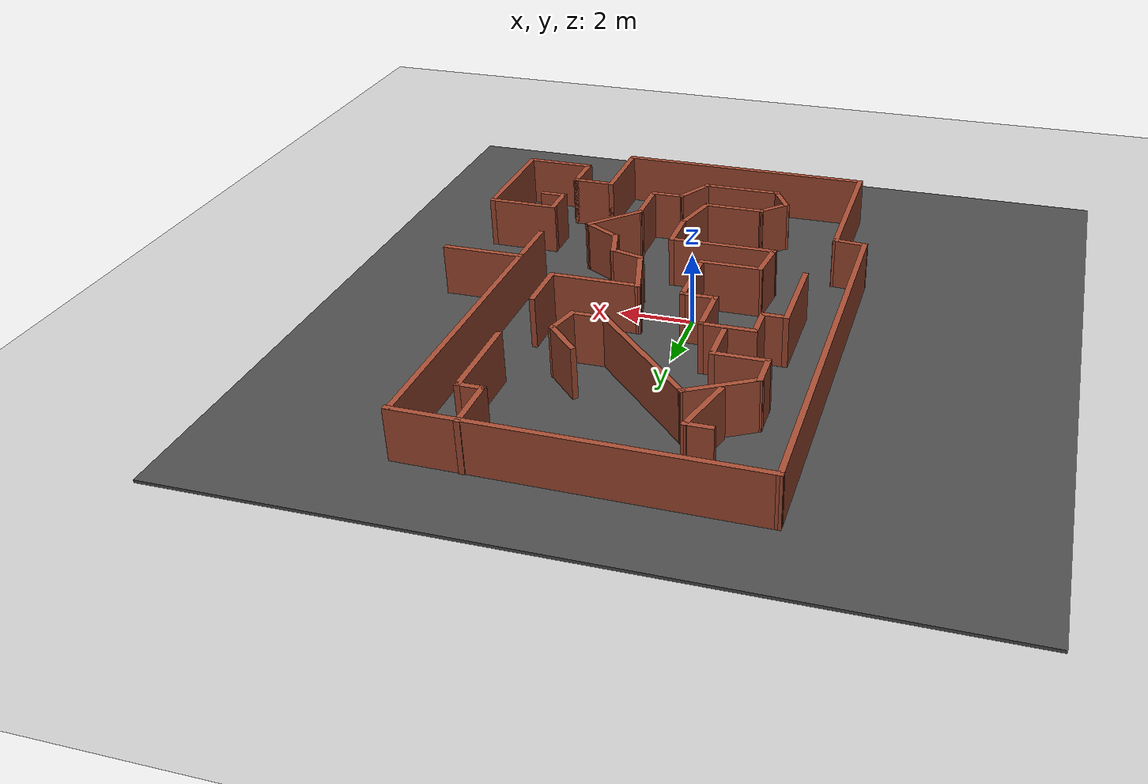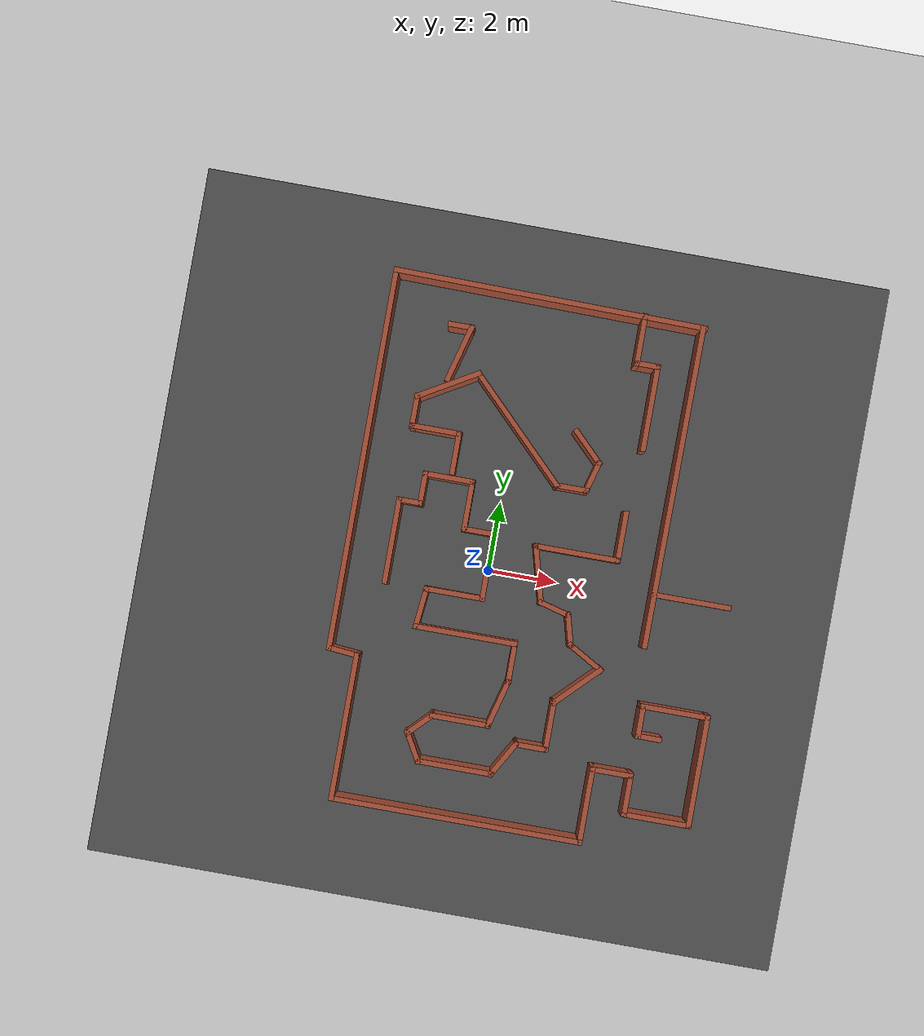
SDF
<sdf version="1.7">
 <world name="expanded_maze_world">
  <light name="sun" type="directional">
   <pose>0 0 10 0 -0 0</pose>
   <diffuse>0.8 0.8 0.8 1</diffuse>
   <specular>0.2 0.2 0.2 1</specular>
   <attenuation>
    <range>1000</range>
    <constant>0.9</constant>
    <linear>0.01</linear>
    <quadratic>0.001</quadratic>
   </attenuation>
   <direction>-0.5 0.1 -0.9</direction>
   <spot><inner_angle>0</inner_angle><outer_angle>0</outer_angle><falloff>0</falloff></spot>
  </light>
  <model name="ground_plane">
   <static>1</static>
   <link name="link">
    <collision name="collision">
     <geometry><plane><normal>0 0 1</normal><size>100 100</size></plane></geometry>
     <surface>
      <contact><collide_bitmask>65535</collide_bitmask></contact>
      <friction><ode><mu>100</mu><mu2>50</mu2></ode></friction>
     </surface>
    </collision>
    <visual name="visual">
     <cast_shadows>0</cast_shadows>
     <geometry><plane><normal>0 0 1</normal><size>100 100</size></plane></geometry>
     <material>
      <script><uri>file://media/materials/scripts/gazebo.material</uri><name>Gazebo/Grey</name></script>
     </material>
    </visual>
   </link>
  </model>
  <model name="ground_plane">
   <static>1</static>
   <link name="link">
    <collision name="collision">
     <geometry><plane><normal>0 0 1</normal><size>100 100</size></plane></geometry>
     <surface>
      <contact><collide_bitmask>65535</collide_bitmask></contact>
      <friction><ode><mu>100</mu><mu2>50</mu2></ode></friction>
     </surface>
    </collision>
    <visual name="visual">
     <cast_shadows>0</cast_shadows>
     <geometry><plane><normal>0 0 1</normal><size>100 100</size></plane></geometry>
     <material>
      <script><uri>file://media/materials/scripts/gazebo.material</uri><name>Gazebo/Grey</name></script>
     </material>
    </visual>
   </link>
  </model>
  <light name="point_light_1" type="point">
   <pose>0 0 10 0 -0 0</pose>
   <diffuse>1 1 1 1</diffuse>
   <specular>0.1 0.1 0.1 1</specular>
   <attenuation>
    <range>20</range>
    <constant>0.5</constant>
    <linear>0.01</linear>
    <quadratic>0.001</quadratic>
   </attenuation>
   <direction>0 0 -1</direction>
   <spot><inner_angle>0</inner_angle><outer_angle>0</outer_angle><falloff>0</falloff></spot>
  </light>
  <gravity>0 0 -9.8</gravity>
  <magnetic_field>6e-06 2.3e-05 -4.2e-05</magnetic_field>
  <atmosphere type="adiabatic"/>
  <physics type="ode">
   <max_step_size>0.001</max_step_size>
   <real_time_factor>1</real_time_factor>
   <real_time_update_rate>1000</real_time_update_rate>
  </physics>
  <scene><ambient>0.4 0.4 0.4 1</ambient><background>0.7 0.7 0.7 1</background><shadows>1</shadows></scene>
  <audio><device>default</device></audio>
  <spherical_coordinates>
   <surface_model>EARTH_WGS84</surface_model>
   <latitude_deg>0</latitude_deg>
   <longitude_deg>0</longitude_deg>
   <elevation>0</elevation>
   <heading_deg>0</heading_deg>
  </spherical_coordinates>
  <model name="Search">
   <link name="Wall_0">
    <pose>-4.64822 -5.4632 0 0 0 -1.5708</pose>
    <visual name="Wall_0_Visual">
     <pose>0 0 1.25 0 -0 0</pose>
     <geometry><box><size>4.25 0.15 2.5</size></box></geometry>
     <material>
      <script><uri>file://media/materials/scripts/gazebo.material</uri><name>Gazebo/Bricks</name></script>
      <ambient>1 1 1 1</ambient>
      <shader type="pixel"/>
     </material>
     <meta><layer>0</layer></meta>
    </visual>
    <collision name="Wall_0_Collision">
     <pose>0 0 1.25 0 -0 0</pose>
     <geometry><box><size>4.25 0.15 2.5</size></box></geometry>
     <surface>
      <friction>
       <ode><mu>1</mu><mu2>1</mu2><fdir1>0 0 0</fdir1><slip1>0</slip1><slip2>0</slip2></ode>
       <torsional>
        <coefficient>1</coefficient>
        <patch_radius>0</patch_radius>
        <surface_radius>0</surface_radius>
        <use_patch_radius>1</use_patch_radius>
        <ode><slip>0</slip></ode>
       </torsional>
      </friction>
      <bounce><restitution_coefficient>0</restitution_coefficient><threshold>1e+06</threshold></bounce>
      <contact>
       <collide_without_contact>0</collide_without_contact>
       <collide_without_contact_bitmask>1</collide_without_contact_bitmask>
       <collide_bitmask>1</collide_bitmask>
       <ode>
        <soft_cfm>0</soft_cfm>
        <soft_erp>0.2</soft_erp>
        <kp>1e+13</kp>
        <kd>1</kd>
        <max_vel>0.01</max_vel>
        <min_depth>0</min_depth>
       </ode>
       <bullet>
        <split_impulse>1</split_impulse>
        <split_impulse_penetration_threshold>-0.01</split_impulse_penetration_threshold>
        <soft_cfm>0</soft_cfm>
        <soft_erp>0.2</soft_erp>
        <kp>1e+13</kp>
        <kd>1</kd>
       </bullet>
      </contact>
     </surface>
    </collision>
   </link>
   <link name="Wall_11">
    <pose>2.4822 -6.4632 0 0 -0 1.5708</pose>
    <visual name="Wall_11_Visual">
     <pose>0 0 1.25 0 -0 0</pose>
     <geometry><box><size>2.25 0.15 2.5</size></box></geometry>
     <material>
      <script><uri>file://media/materials/scripts/gazebo.material</uri><name>Gazebo/Bricks</name></script>
      <ambient>1 1 1 1</ambient>
      <shader type="pixel"/>
     </material>
     <meta><layer>0</layer></meta>
    </visual>
    <collision name="Wall_11_Collision">
     <pose>0 0 1.25 0 -0 0</pose>
     <geometry><box><size>2.25 0.15 2.5</size></box></geometry>
     <surface>
      <friction>
       <ode><mu>1</mu><mu2>1</mu2><fdir1>0 0 0</fdir1><slip1>0</slip1><slip2>0</slip2></ode>
       <torsional>
        <coefficient>1</coefficient>
        <patch_radius>0</patch_radius>
        <surface_radius>0</surface_radius>
        <use_patch_radius>1</use_patch_radius>
        <ode><slip>0</slip></ode>
       </torsional>
      </friction>
      <bounce><restitution_coefficient>0</restitution_coefficient><threshold>1e+06</threshold></bounce>
      <contact>
       <collide_without_contact>0</collide_without_contact>
       <collide_without_contact_bitmask>1</collide_without_contact_bitmask>
       <collide_bitmask>1</collide_bitmask>
       <ode>
        <soft_cfm>0</soft_cfm>
        <soft_erp>0.2</soft_erp>
        <kp>1e+13</kp>
        <kd>1</kd>
        <max_vel>0.01</max_vel>
        <min_depth>0</min_depth>
       </ode>
       <bullet>
        <split_impulse>1</split_impulse>
        <split_impulse_penetration_threshold>-0.01</split_impulse_penetration_threshold>
        <soft_cfm>0</soft_cfm>
        <soft_erp>0.2</soft_erp>
        <kp>1e+13</kp>
        <kd>1</kd>
       </bullet>
      </contact>
     </surface>
    </collision>
   </link>
   <link name="Wall_12">
    <pose>3.0322 -5.4132 0 0 -0 0</pose>
    <visual name="Wall_12_Visual">
     <pose>0 0 1.25 0 -0 0</pose>
     <geometry><box><size>1.25 0.15 2.5</size></box></geometry>
     <material>
      <script><uri>file://media/materials/scripts/gazebo.material</uri><name>Gazebo/Bricks</name></script>
      <ambient>1 1 1 1</ambient>
      <shader type="pixel"/>
     </material>
     <meta><layer>0</layer></meta>
    </visual>
    <collision name="Wall_12_Collision">
     <pose>0 0 1.25 0 -0 0</pose>
     <geometry><box><size>1.25 0.15 2.5</size></box></geometry>
     <surface>
      <friction>
       <ode><mu>1</mu><mu2>1</mu2><fdir1>0 0 0</fdir1><slip1>0</slip1><slip2>0</slip2></ode>
       <torsional>
        <coefficient>1</coefficient>
        <patch_radius>0</patch_radius>
        <surface_radius>0</surface_radius>
        <use_patch_radius>1</use_patch_radius>
        <ode><slip>0</slip></ode>
       </torsional>
      </friction>
      <bounce><restitution_coefficient>0</restitution_coefficient><threshold>1e+06</threshold></bounce>
      <contact>
       <collide_without_contact>0</collide_without_contact>
       <collide_without_contact_bitmask>1</collide_without_contact_bitmask>
       <collide_bitmask>1</collide_bitmask>
       <ode>
        <soft_cfm>0</soft_cfm>
        <soft_erp>0.2</soft_erp>
        <kp>1e+13</kp>
        <kd>1</kd>
        <max_vel>0.01</max_vel>
        <min_depth>0</min_depth>
       </ode>
       <bullet>
        <split_impulse>1</split_impulse>
        <split_impulse_penetration_threshold>-0.01</split_impulse_penetration_threshold>
        <soft_cfm>0</soft_cfm>
        <soft_erp>0.2</soft_erp>
        <kp>1e+13</kp>
        <kd>1</kd>
       </bullet>
      </contact>
     </surface>
    </collision>
   </link>
   <link name="Wall_13">
    <pose>3.5822 -5.9632 0 0 0 -1.5708</pose>
    <visual name="Wall_13_Visual">
     <pose>0 0 1.25 0 -0 0</pose>
     <geometry><box><size>1.25 0.15 2.5</size></box></geometry>
     <material>
      <script><uri>file://media/materials/scripts/gazebo.material</uri><name>Gazebo/Bricks</name></script>
      <ambient>1 1 1 1</ambient>
      <shader type="pixel"/>
     </material>
     <meta><layer>0</layer></meta>
    </visual>
    <collision name="Wall_13_Collision">
     <pose>0 0 1.25 0 -0 0</pose>
     <geometry><box><size>1.25 0.15 2.5</size></box></geometry>
     <surface>
      <friction>
       <ode><mu>1</mu><mu2>1</mu2><fdir1>0 0 0</fdir1><slip1>0</slip1><slip2>0</slip2></ode>
       <torsional>
        <coefficient>1</coefficient>
        <patch_radius>0</patch_radius>
        <surface_radius>0</surface_radius>
        <use_patch_radius>1</use_patch_radius>
        <ode><slip>0</slip></ode>
       </torsional>
      </friction>
      <bounce><restitution_coefficient>0</restitution_coefficient><threshold>1e+06</threshold></bounce>
      <contact>
       <collide_without_contact>0</collide_without_contact>
       <collide_without_contact_bitmask>1</collide_without_contact_bitmask>
       <collide_bitmask>1</collide_bitmask>
       <ode>
        <soft_cfm>0</soft_cfm>
        <soft_erp>0.2</soft_erp>
        <kp>1e+13</kp>
        <kd>1</kd>
        <max_vel>0.01</max_vel>
        <min_depth>0</min_depth>
       </ode>
       <bullet>
        <split_impulse>1</split_impulse>
        <split_impulse_penetration_threshold>-0.01</split_impulse_penetration_threshold>
        <soft_cfm>0</soft_cfm>
        <soft_erp>0.2</soft_erp>
        <kp>1e+13</kp>
        <kd>1</kd>
       </bullet>
      </contact>
     </surface>
    </collision>
   </link>
   <link name="Wall_14">
    <pose>4.5072 -6.5132 0 0 -0 0</pose>
    <visual name="Wall_14_Visual">
     <pose>0 0 1.25 0 -0 0</pose>
     <geometry><box><size>2 0.15 2.5</size></box></geometry>
     <material>
      <script><uri>file://media/materials/scripts/gazebo.material</uri><name>Gazebo/Bricks</name></script>
      <ambient>1 1 1 1</ambient>
      <shader type="pixel"/>
     </material>
     <meta><layer>0</layer></meta>
    </visual>
    <collision name="Wall_14_Collision">
     <pose>0 0 1.25 0 -0 0</pose>
     <geometry><box><size>2 0.15 2.5</size></box></geometry>
     <surface>
      <friction>
       <ode><mu>1</mu><mu2>1</mu2><fdir1>0 0 0</fdir1><slip1>0</slip1><slip2>0</slip2></ode>
       <torsional>
        <coefficient>1</coefficient>
        <patch_radius>0</patch_radius>
        <surface_radius>0</surface_radius>
        <use_patch_radius>1</use_patch_radius>
        <ode><slip>0</slip></ode>
       </torsional>
      </friction>
      <bounce><restitution_coefficient>0</restitution_coefficient><threshold>1e+06</threshold></bounce>
      <contact>
       <collide_without_contact>0</collide_without_contact>
       <collide_without_contact_bitmask>1</collide_without_contact_bitmask>
       <collide_bitmask>1</collide_bitmask>
       <ode>
        <soft_cfm>0</soft_cfm>
        <soft_erp>0.2</soft_erp>
        <kp>1e+13</kp>
        <kd>1</kd>
        <max_vel>0.01</max_vel>
        <min_depth>0</min_depth>
       </ode>
       <bullet>
        <split_impulse>1</split_impulse>
        <split_impulse_penetration_threshold>-0.01</split_impulse_penetration_threshold>
        <soft_cfm>0</soft_cfm>
        <soft_erp>0.2</soft_erp>
        <kp>1e+13</kp>
        <kd>1</kd>
       </bullet>
      </contact>
     </surface>
    </collision>
   </link>
   <link name="Wall_15">
    <pose>5.4322 -4.9632 0 0 -0 1.5708</pose>
    <visual name="Wall_15_Visual">
     <pose>0 0 1.25 0 -0 0</pose>
     <geometry><box><size>3.25 0.15 2.5</size></box></geometry>
     <material>
      <script><uri>file://media/materials/scripts/gazebo.material</uri><name>Gazebo/Bricks</name></script>
      <ambient>1 1 1 1</ambient>
      <shader type="pixel"/>
     </material>
     <meta><layer>0</layer></meta>
    </visual>
    <collision name="Wall_15_Collision">
     <pose>0 0 1.25 0 -0 0</pose>
     <geometry><box><size>3.25 0.15 2.5</size></box></geometry>
     <surface>
      <friction>
       <ode><mu>1</mu><mu2>1</mu2><fdir1>0 0 0</fdir1><slip1>0</slip1><slip2>0</slip2></ode>
       <torsional>
        <coefficient>1</coefficient>
        <patch_radius>0</patch_radius>
        <surface_radius>0</surface_radius>
        <use_patch_radius>1</use_patch_radius>
        <ode><slip>0</slip></ode>
       </torsional>
      </friction>
      <bounce><restitution_coefficient>0</restitution_coefficient><threshold>1e+06</threshold></bounce>
      <contact>
       <collide_without_contact>0</collide_without_contact>
       <collide_without_contact_bitmask>1</collide_without_contact_bitmask>
       <collide_bitmask>1</collide_bitmask>
       <ode>
        <soft_cfm>0</soft_cfm>
        <soft_erp>0.2</soft_erp>
        <kp>1e+13</kp>
        <kd>1</kd>
        <max_vel>0.01</max_vel>
        <min_depth>0</min_depth>
       </ode>
       <bullet>
        <split_impulse>1</split_impulse>
        <split_impulse_penetration_threshold>-0.01</split_impulse_penetration_threshold>
        <soft_cfm>0</soft_cfm>
        <soft_erp>0.2</soft_erp>
        <kp>1e+13</kp>
        <kd>1</kd>
       </bullet>
      </contact>
     </surface>
    </collision>
   </link>
   <link name="Wall_16">
    <pose>4.5072 -3.4132 0 0 -0 3.14159</pose>
    <visual name="Wall_16_Visual">
     <pose>0 0 1.25 0 -0 0</pose>
     <geometry><box><size>2 0.15 2.5</size></box></geometry>
     <material>
      <script><uri>file://media/materials/scripts/gazebo.material</uri><name>Gazebo/Bricks</name></script>
      <ambient>1 1 1 1</ambient>
      <shader type="pixel"/>
     </material>
     <meta><layer>0</layer></meta>
    </visual>
    <collision name="Wall_16_Collision">
     <pose>0 0 1.25 0 -0 0</pose>
     <geometry><box><size>2 0.15 2.5</size></box></geometry>
     <surface>
      <friction>
       <ode><mu>1</mu><mu2>1</mu2><fdir1>0 0 0</fdir1><slip1>0</slip1><slip2>0</slip2></ode>
       <torsional>
        <coefficient>1</coefficient>
        <patch_radius>0</patch_radius>
        <surface_radius>0</surface_radius>
        <use_patch_radius>1</use_patch_radius>
        <ode><slip>0</slip></ode>
       </torsional>
      </friction>
      <bounce><restitution_coefficient>0</restitution_coefficient><threshold>1e+06</threshold></bounce>
      <contact>
       <collide_without_contact>0</collide_without_contact>
       <collide_without_contact_bitmask>1</collide_without_contact_bitmask>
       <collide_bitmask>1</collide_bitmask>
       <ode>
        <soft_cfm>0</soft_cfm>
        <soft_erp>0.2</soft_erp>
        <kp>1e+13</kp>
        <kd>1</kd>
        <max_vel>0.01</max_vel>
        <min_depth>0</min_depth>
       </ode>
       <bullet>
        <split_impulse>1</split_impulse>
        <split_impulse_penetration_threshold>-0.01</split_impulse_penetration_threshold>
        <soft_cfm>0</soft_cfm>
        <soft_erp>0.2</soft_erp>
        <kp>1e+13</kp>
        <kd>1</kd>
       </bullet>
      </contact>
     </surface>
    </collision>
   </link>
   <link name="Wall_17">
    <pose>3.5822 -3.8382 0 0 0 -1.5708</pose>
    <visual name="Wall_17_Visual">
     <pose>0 0 1.25 0 -0 0</pose>
     <geometry><box><size>1 0.15 2.5</size></box></geometry>
     <material>
      <script><uri>file://media/materials/scripts/gazebo.material</uri><name>Gazebo/Bricks</name></script>
      <ambient>1 1 1 1</ambient>
      <shader type="pixel"/>
     </material>
     <meta><layer>0</layer></meta>
    </visual>
    <collision name="Wall_17_Collision">
     <pose>0 0 1.25 0 -0 0</pose>
     <geometry><box><size>1 0.15 2.5</size></box></geometry>
     <surface>
      <friction>
       <ode><mu>1</mu><mu2>1</mu2><fdir1>0 0 0</fdir1><slip1>0</slip1><slip2>0</slip2></ode>
       <torsional>
        <coefficient>1</coefficient>
        <patch_radius>0</patch_radius>
        <surface_radius>0</surface_radius>
        <use_patch_radius>1</use_patch_radius>
        <ode><slip>0</slip></ode>
       </torsional>
      </friction>
      <bounce><restitution_coefficient>0</restitution_coefficient><threshold>1e+06</threshold></bounce>
      <contact>
       <collide_without_contact>0</collide_without_contact>
       <collide_without_contact_bitmask>1</collide_without_contact_bitmask>
       <collide_bitmask>1</collide_bitmask>
       <ode>
        <soft_cfm>0</soft_cfm>
        <soft_erp>0.2</soft_erp>
        <kp>1e+13</kp>
        <kd>1</kd>
        <max_vel>0.01</max_vel>
        <min_depth>0</min_depth>
       </ode>
       <bullet>
        <split_impulse>1</split_impulse>
        <split_impulse_penetration_threshold>-0.01</split_impulse_penetration_threshold>
        <soft_cfm>0</soft_cfm>
        <soft_erp>0.2</soft_erp>
        <kp>1e+13</kp>
        <kd>1</kd>
       </bullet>
      </contact>
     </surface>
    </collision>
   </link>
   <link name="Wall_18">
    <pose>3.8822 -4.2632 0 0 -0 0</pose>
    <visual name="Wall_18_Visual">
     <pose>0 0 1.25 0 -0 0</pose>
     <geometry><box><size>0.75 0.15 2.5</size></box></geometry>
     <material>
      <script><uri>file://media/materials/scripts/gazebo.material</uri><name>Gazebo/Bricks</name></script>
      <ambient>1 1 1 1</ambient>
      <shader type="pixel"/>
     </material>
     <meta><layer>0</layer></meta>
    </visual>
    <collision name="Wall_18_Collision">
     <pose>0 0 1.25 0 -0 0</pose>
     <geometry><box><size>0.75 0.15 2.5</size></box></geometry>
     <surface>
      <friction>
       <ode><mu>1</mu><mu2>1</mu2><fdir1>0 0 0</fdir1><slip1>0</slip1><slip2>0</slip2></ode>
       <torsional>
        <coefficient>1</coefficient>
        <patch_radius>0</patch_radius>
        <surface_radius>0</surface_radius>
        <use_patch_radius>1</use_patch_radius>
        <ode><slip>0</slip></ode>
       </torsional>
      </friction>
      <bounce><restitution_coefficient>0</restitution_coefficient><threshold>1e+06</threshold></bounce>
      <contact>
       <collide_without_contact>0</collide_without_contact>
       <collide_without_contact_bitmask>1</collide_without_contact_bitmask>
       <collide_bitmask>1</collide_bitmask>
       <ode>
        <soft_cfm>0</soft_cfm>
        <soft_erp>0.2</soft_erp>
        <kp>1e+13</kp>
        <kd>1</kd>
        <max_vel>0.01</max_vel>
        <min_depth>0</min_depth>
       </ode>
       <bullet>
        <split_impulse>1</split_impulse>
        <split_impulse_penetration_threshold>-0.01</split_impulse_penetration_threshold>
        <soft_cfm>0</soft_cfm>
        <soft_erp>0.2</soft_erp>
        <kp>1e+13</kp>
        <kd>1</kd>
       </bullet>
      </contact>
     </surface>
    </collision>
   </link>
   <link name="Wall_23">
    <pose>3.35084 2.83731 0 0 -0 1.56494</pose>
    <visual name="Wall_23_Visual">
     <pose>0 0 1.25 0 -0 0</pose>
     <geometry><box><size>9.28615 0.15 2.5</size></box></geometry>
     <material>
      <script><uri>file://media/materials/scripts/gazebo.material</uri><name>Gazebo/Bricks</name></script>
      <ambient>1 1 1 1</ambient>
      <shader type="pixel"/>
     </material>
     <meta><layer>0</layer></meta>
    </visual>
    <collision name="Wall_23_Collision">
     <pose>0 0 1.25 0 -0 0</pose>
     <geometry><box><size>9.28615 0.15 2.5</size></box></geometry>
     <surface>
      <friction>
       <ode><mu>1</mu><mu2>1</mu2><fdir1>0 0 0</fdir1><slip1>0</slip1><slip2>0</slip2></ode>
       <torsional>
        <coefficient>1</coefficient>
        <patch_radius>0</patch_radius>
        <surface_radius>0</surface_radius>
        <use_patch_radius>1</use_patch_radius>
        <ode><slip>0</slip></ode>
       </torsional>
      </friction>
      <bounce><restitution_coefficient>0</restitution_coefficient><threshold>1e+06</threshold></bounce>
      <contact>
       <collide_without_contact>0</collide_without_contact>
       <collide_without_contact_bitmask>1</collide_without_contact_bitmask>
       <collide_bitmask>1</collide_bitmask>
       <ode>
        <soft_cfm>0</soft_cfm>
        <soft_erp>0.2</soft_erp>
        <kp>1e+13</kp>
        <kd>1</kd>
        <max_vel>0.01</max_vel>
        <min_depth>0</min_depth>
       </ode>
       <bullet>
        <split_impulse>1</split_impulse>
        <split_impulse_penetration_threshold>-0.01</split_impulse_penetration_threshold>
        <soft_cfm>0</soft_cfm>
        <soft_erp>0.2</soft_erp>
        <kp>1e+13</kp>
        <kd>1</kd>
       </bullet>
      </contact>
     </surface>
    </collision>
   </link>
   <link name="Wall_24">
    <pose>-1.0119 7.4588 0 0 -0 3.12955</pose>
    <visual name="Wall_24_Visual">
     <pose>0 0 1.25 0 -0 0</pose>
     <geometry><box><size>9.03663 0.15 2.5</size></box></geometry>
     <material>
      <script><uri>file://media/materials/scripts/gazebo.material</uri><name>Gazebo/Bricks</name></script>
      <ambient>1 1 1 1</ambient>
      <shader type="pixel"/>
     </material>
     <meta><layer>0</layer></meta>
    </visual>
    <collision name="Wall_24_Collision">
     <pose>0 0 1.25 0 -0 0</pose>
     <geometry><box><size>9.03663 0.15 2.5</size></box></geometry>
     <surface>
      <friction>
       <ode><mu>1</mu><mu2>1</mu2><fdir1>0 0 0</fdir1><slip1>0</slip1><slip2>0</slip2></ode>
       <torsional>
        <coefficient>1</coefficient>
        <patch_radius>0</patch_radius>
        <surface_radius>0</surface_radius>
        <use_patch_radius>1</use_patch_radius>
        <ode><slip>0</slip></ode>
       </torsional>
      </friction>
      <bounce><restitution_coefficient>0</restitution_coefficient><threshold>1e+06</threshold></bounce>
      <contact>
       <collide_without_contact>0</collide_without_contact>
       <collide_without_contact_bitmask>1</collide_without_contact_bitmask>
       <collide_bitmask>1</collide_bitmask>
       <ode>
        <soft_cfm>0</soft_cfm>
        <soft_erp>0.2</soft_erp>
        <kp>1e+13</kp>
        <kd>1</kd>
        <max_vel>0.01</max_vel>
        <min_depth>0</min_depth>
       </ode>
       <bullet>
        <split_impulse>1</split_impulse>
        <split_impulse_penetration_threshold>-0.01</split_impulse_penetration_threshold>
        <soft_cfm>0</soft_cfm>
        <soft_erp>0.2</soft_erp>
        <kp>1e+13</kp>
        <kd>1</kd>
       </bullet>
      </contact>
     </surface>
    </collision>
   </link>
   <link name="Wall_25">
    <pose>-5.45489 2.08731 0 0 0 -1.5708</pose>
    <visual name="Wall_25_Visual">
     <pose>0 0 1.25 0 -0 0</pose>
     <geometry><box><size>11 0.15 2.5</size></box></geometry>
     <material>
      <script><uri>file://media/materials/scripts/gazebo.material</uri><name>Gazebo/Bricks</name></script>
      <ambient>1 1 1 1</ambient>
      <shader type="pixel"/>
     </material>
     <meta><layer>0</layer></meta>
    </visual>
    <collision name="Wall_25_Collision">
     <pose>0 0 1.25 0 -0 0</pose>
     <geometry><box><size>11 0.15 2.5</size></box></geometry>
     <surface>
      <friction>
       <ode><mu>1</mu><mu2>1</mu2><fdir1>0 0 0</fdir1><slip1>0</slip1><slip2>0</slip2></ode>
       <torsional>
        <coefficient>1</coefficient>
        <patch_radius>0</patch_radius>
        <surface_radius>0</surface_radius>
        <use_patch_radius>1</use_patch_radius>
        <ode><slip>0</slip></ode>
       </torsional>
      </friction>
      <bounce><restitution_coefficient>0</restitution_coefficient><threshold>1e+06</threshold></bounce>
      <contact>
       <collide_without_contact>0</collide_without_contact>
       <collide_without_contact_bitmask>1</collide_without_contact_bitmask>
       <collide_bitmask>1</collide_bitmask>
       <ode>
        <soft_cfm>0</soft_cfm>
        <soft_erp>0.2</soft_erp>
        <kp>1e+13</kp>
        <kd>1</kd>
        <max_vel>0.01</max_vel>
        <min_depth>0</min_depth>
       </ode>
       <bullet>
        <split_impulse>1</split_impulse>
        <split_impulse_penetration_threshold>-0.01</split_impulse_penetration_threshold>
        <soft_cfm>0</soft_cfm>
        <soft_erp>0.2</soft_erp>
        <kp>1e+13</kp>
        <kd>1</kd>
       </bullet>
      </contact>
     </surface>
    </collision>
   </link>
   <link name="Wall_26">
    <pose>-5.05155 -3.37545 0 0 0 -0.093331</pose>
    <visual name="Wall_26_Visual">
     <pose>0 0 1.25 0 -0 0</pose>
     <geometry><box><size>0.960202 0.15 2.5</size></box></geometry>
     <material>
      <script><uri>file://media/materials/scripts/gazebo.material</uri><name>Gazebo/Bricks</name></script>
      <ambient>1 1 1 1</ambient>
      <shader type="pixel"/>
     </material>
     <meta><layer>0</layer></meta>
    </visual>
    <collision name="Wall_26_Collision">
     <pose>0 0 1.25 0 -0 0</pose>
     <geometry><box><size>0.960202 0.15 2.5</size></box></geometry>
     <surface>
      <friction>
       <ode><mu>1</mu><mu2>1</mu2><fdir1>0 0 0</fdir1><slip1>0</slip1><slip2>0</slip2></ode>
       <torsional>
        <coefficient>1</coefficient>
        <patch_radius>0</patch_radius>
        <surface_radius>0</surface_radius>
        <use_patch_radius>1</use_patch_radius>
        <ode><slip>0</slip></ode>
       </torsional>
      </friction>
      <bounce><restitution_coefficient>0</restitution_coefficient><threshold>1e+06</threshold></bounce>
      <contact>
       <collide_without_contact>0</collide_without_contact>
       <collide_without_contact_bitmask>1</collide_without_contact_bitmask>
       <collide_bitmask>1</collide_bitmask>
       <ode>
        <soft_cfm>0</soft_cfm>
        <soft_erp>0.2</soft_erp>
        <kp>1e+13</kp>
        <kd>1</kd>
        <max_vel>0.01</max_vel>
        <min_depth>0</min_depth>
       </ode>
       <bullet>
        <split_impulse>1</split_impulse>
        <split_impulse_penetration_threshold>-0.01</split_impulse_penetration_threshold>
        <soft_cfm>0</soft_cfm>
        <soft_erp>0.2</soft_erp>
        <kp>1e+13</kp>
        <kd>1</kd>
       </bullet>
      </contact>
     </surface>
    </collision>
   </link>
   <link name="Wall_28">
    <pose>4.41155 -0.253683 0 0 -0 0</pose>
    <visual name="Wall_28_Visual">
     <pose>0 0 1.25 0 -0 0</pose>
     <geometry><box><size>2.25 0.15 2.5</size></box></geometry>
     <material>
      <script><uri>file://media/materials/scripts/gazebo.material</uri><name>Gazebo/Bricks</name></script>
      <ambient>1 1 1 1</ambient>
      <shader type="pixel"/>
     </material>
     <meta><layer>0</layer></meta>
    </visual>
    <collision name="Wall_28_Collision">
     <pose>0 0 1.25 0 -0 0</pose>
     <geometry><box><size>2.25 0.15 2.5</size></box></geometry>
     <surface>
      <friction>
       <ode><mu>1</mu><mu2>1</mu2><fdir1>0 0 0</fdir1><slip1>0</slip1><slip2>0</slip2></ode>
       <torsional>
        <coefficient>1</coefficient>
        <patch_radius>0</patch_radius>
        <surface_radius>0</surface_radius>
        <use_patch_radius>1</use_patch_radius>
        <ode><slip>0</slip></ode>
       </torsional>
      </friction>
      <bounce><restitution_coefficient>0</restitution_coefficient><threshold>1e+06</threshold></bounce>
      <contact>
       <collide_without_contact>0</collide_without_contact>
       <collide_without_contact_bitmask>1</collide_without_contact_bitmask>
       <collide_bitmask>1</collide_bitmask>
       <ode>
        <soft_cfm>0</soft_cfm>
        <soft_erp>0.2</soft_erp>
        <kp>1e+13</kp>
        <kd>1</kd>
        <max_vel>0.01</max_vel>
        <min_depth>0</min_depth>
       </ode>
       <bullet>
        <split_impulse>1</split_impulse>
        <split_impulse_penetration_threshold>-0.01</split_impulse_penetration_threshold>
        <soft_cfm>0</soft_cfm>
        <soft_erp>0.2</soft_erp>
        <kp>1e+13</kp>
        <kd>1</kd>
       </bullet>
      </contact>
     </surface>
    </collision>
   </link>
   <link name="Wall_30">
    <pose>-4.2358 -0.041728 0 0 -0 1.5708</pose>
    <visual name="Wall_30_Visual">
     <pose>0 0 1.25 0 -0 0</pose>
     <geometry><box><size>2.5 0.15 2.5</size></box></geometry>
     <material>
      <script><uri>file://media/materials/scripts/gazebo.material</uri><name>Gazebo/Bricks</name></script>
      <ambient>1 1 1 1</ambient>
      <shader type="pixel"/>
     </material>
     <meta><layer>0</layer></meta>
    </visual>
    <collision name="Wall_30_Collision">
     <pose>0 0 1.25 0 -0 0</pose>
     <geometry><box><size>2.5 0.15 2.5</size></box></geometry>
     <surface>
      <friction>
       <ode><mu>1</mu><mu2>1</mu2><fdir1>0 0 0</fdir1><slip1>0</slip1><slip2>0</slip2></ode>
       <torsional>
        <coefficient>1</coefficient>
        <patch_radius>0</patch_radius>
        <surface_radius>0</surface_radius>
        <use_patch_radius>1</use_patch_radius>
        <ode><slip>0</slip></ode>
       </torsional>
      </friction>
      <bounce><restitution_coefficient>0</restitution_coefficient><threshold>1e+06</threshold></bounce>
      <contact>
       <collide_without_contact>0</collide_without_contact>
       <collide_without_contact_bitmask>1</collide_without_contact_bitmask>
       <collide_bitmask>1</collide_bitmask>
       <ode>
        <soft_cfm>0</soft_cfm>
        <soft_erp>0.2</soft_erp>
        <kp>1e+13</kp>
        <kd>1</kd>
        <max_vel>0.01</max_vel>
        <min_depth>0</min_depth>
       </ode>
       <bullet>
        <split_impulse>1</split_impulse>
        <split_impulse_penetration_threshold>-0.01</split_impulse_penetration_threshold>
        <soft_cfm>0</soft_cfm>
        <soft_erp>0.2</soft_erp>
        <kp>1e+13</kp>
        <kd>1</kd>
       </bullet>
      </contact>
     </surface>
    </collision>
   </link>
   <link name="Wall_31">
    <pose>-3.9358 1.13327 0 0 -0 0</pose>
    <visual name="Wall_31_Visual">
     <pose>0 0 1.25 0 -0 0</pose>
     <geometry><box><size>0.75 0.15 2.5</size></box></geometry>
     <material>
      <script><uri>file://media/materials/scripts/gazebo.material</uri><name>Gazebo/Bricks</name></script>
      <ambient>1 1 1 1</ambient>
      <shader type="pixel"/>
     </material>
     <meta><layer>0</layer></meta>
    </visual>
    <collision name="Wall_31_Collision">
     <pose>0 0 1.25 0 -0 0</pose>
     <geometry><box><size>0.75 0.15 2.5</size></box></geometry>
     <surface>
      <friction>
       <ode><mu>1</mu><mu2>1</mu2><fdir1>0 0 0</fdir1><slip1>0</slip1><slip2>0</slip2></ode>
       <torsional>
        <coefficient>1</coefficient>
        <patch_radius>0</patch_radius>
        <surface_radius>0</surface_radius>
        <use_patch_radius>1</use_patch_radius>
        <ode><slip>0</slip></ode>
       </torsional>
      </friction>
      <bounce><restitution_coefficient>0</restitution_coefficient><threshold>1e+06</threshold></bounce>
      <contact>
       <collide_without_contact>0</collide_without_contact>
       <collide_without_contact_bitmask>1</collide_without_contact_bitmask>
       <collide_bitmask>1</collide_bitmask>
       <ode>
        <soft_cfm>0</soft_cfm>
        <soft_erp>0.2</soft_erp>
        <kp>1e+13</kp>
        <kd>1</kd>
        <max_vel>0.01</max_vel>
        <min_depth>0</min_depth>
       </ode>
       <bullet>
        <split_impulse>1</split_impulse>
        <split_impulse_penetration_threshold>-0.01</split_impulse_penetration_threshold>
        <soft_cfm>0</soft_cfm>
        <soft_erp>0.2</soft_erp>
        <kp>1e+13</kp>
        <kd>1</kd>
       </bullet>
      </contact>
     </surface>
    </collision>
   </link>
   <link name="Wall_32">
    <pose>-3.6358 1.55827 0 0 -0 1.5708</pose>
    <visual name="Wall_32_Visual">
     <pose>0 0 1.25 0 -0 0</pose>
     <geometry><box><size>1 0.15 2.5</size></box></geometry>
     <material>
      <script><uri>file://media/materials/scripts/gazebo.material</uri><name>Gazebo/Bricks</name></script>
      <ambient>1 1 1 1</ambient>
      <shader type="pixel"/>
     </material>
     <meta><layer>0</layer></meta>
    </visual>
    <collision name="Wall_32_Collision">
     <pose>0 0 1.25 0 -0 0</pose>
     <geometry><box><size>1 0.15 2.5</size></box></geometry>
     <surface>
      <friction>
       <ode><mu>1</mu><mu2>1</mu2><fdir1>0 0 0</fdir1><slip1>0</slip1><slip2>0</slip2></ode>
       <torsional>
        <coefficient>1</coefficient>
        <patch_radius>0</patch_radius>
        <surface_radius>0</surface_radius>
        <use_patch_radius>1</use_patch_radius>
        <ode><slip>0</slip></ode>
       </torsional>
      </friction>
      <bounce><restitution_coefficient>0</restitution_coefficient><threshold>1e+06</threshold></bounce>
      <contact>
       <collide_without_contact>0</collide_without_contact>
       <collide_without_contact_bitmask>1</collide_without_contact_bitmask>
       <collide_bitmask>1</collide_bitmask>
       <ode>
        <soft_cfm>0</soft_cfm>
        <soft_erp>0.2</soft_erp>
        <kp>1e+13</kp>
        <kd>1</kd>
        <max_vel>0.01</max_vel>
        <min_depth>0</min_depth>
       </ode>
       <bullet>
        <split_impulse>1</split_impulse>
        <split_impulse_penetration_threshold>-0.01</split_impulse_penetration_threshold>
        <soft_cfm>0</soft_cfm>
        <soft_erp>0.2</soft_erp>
        <kp>1e+13</kp>
        <kd>1</kd>
       </bullet>
      </contact>
     </surface>
    </collision>
   </link>
   <link name="Wall_33">
    <pose>-2.9608 1.98327 0 0 -0 0</pose>
    <visual name="Wall_33_Visual">
     <pose>0 0 1.25 0 -0 0</pose>
     <geometry><box><size>1.5 0.15 2.5</size></box></geometry>
     <material>
      <script><uri>file://media/materials/scripts/gazebo.material</uri><name>Gazebo/Bricks</name></script>
      <ambient>1 1 1 1</ambient>
      <shader type="pixel"/>
     </material>
     <meta><layer>0</layer></meta>
    </visual>
    <collision name="Wall_33_Collision">
     <pose>0 0 1.25 0 -0 0</pose>
     <geometry><box><size>1.5 0.15 2.5</size></box></geometry>
     <surface>
      <friction>
       <ode><mu>1</mu><mu2>1</mu2><fdir1>0 0 0</fdir1><slip1>0</slip1><slip2>0</slip2></ode>
       <torsional>
        <coefficient>1</coefficient>
        <patch_radius>0</patch_radius>
        <surface_radius>0</surface_radius>
        <use_patch_radius>1</use_patch_radius>
        <ode><slip>0</slip></ode>
       </torsional>
      </friction>
      <bounce><restitution_coefficient>0</restitution_coefficient><threshold>1e+06</threshold></bounce>
      <contact>
       <collide_without_contact>0</collide_without_contact>
       <collide_without_contact_bitmask>1</collide_without_contact_bitmask>
       <collide_bitmask>1</collide_bitmask>
       <ode>
        <soft_cfm>0</soft_cfm>
        <soft_erp>0.2</soft_erp>
        <kp>1e+13</kp>
        <kd>1</kd>
        <max_vel>0.01</max_vel>
        <min_depth>0</min_depth>
       </ode>
       <bullet>
        <split_impulse>1</split_impulse>
        <split_impulse_penetration_threshold>-0.01</split_impulse_penetration_threshold>
        <soft_cfm>0</soft_cfm>
        <soft_erp>0.2</soft_erp>
        <kp>1e+13</kp>
        <kd>1</kd>
       </bullet>
      </contact>
     </surface>
    </collision>
   </link>
   <link name="Wall_34">
    <pose>-2.2858 1.30827 0 0 0 -1.5708</pose>
    <visual name="Wall_34_Visual">
     <pose>0 0 1.25 0 -0 0</pose>
     <geometry><box><size>1.5 0.15 2.5</size></box></geometry>
     <material>
      <script><uri>file://media/materials/scripts/gazebo.material</uri><name>Gazebo/Bricks</name></script>
      <ambient>1 1 1 1</ambient>
      <shader type="pixel"/>
     </material>
     <meta><layer>0</layer></meta>
    </visual>
    <collision name="Wall_34_Collision">
     <pose>0 0 1.25 0 -0 0</pose>
     <geometry><box><size>1.5 0.15 2.5</size></box></geometry>
     <surface>
      <friction>
       <ode><mu>1</mu><mu2>1</mu2><fdir1>0 0 0</fdir1><slip1>0</slip1><slip2>0</slip2></ode>
       <torsional>
        <coefficient>1</coefficient>
        <patch_radius>0</patch_radius>
        <surface_radius>0</surface_radius>
        <use_patch_radius>1</use_patch_radius>
        <ode><slip>0</slip></ode>
       </torsional>
      </friction>
      <bounce><restitution_coefficient>0</restitution_coefficient><threshold>1e+06</threshold></bounce>
      <contact>
       <collide_without_contact>0</collide_without_contact>
       <collide_without_contact_bitmask>1</collide_without_contact_bitmask>
       <collide_bitmask>1</collide_bitmask>
       <ode>
        <soft_cfm>0</soft_cfm>
        <soft_erp>0.2</soft_erp>
        <kp>1e+13</kp>
        <kd>1</kd>
        <max_vel>0.01</max_vel>
        <min_depth>0</min_depth>
       </ode>
       <bullet>
        <split_impulse>1</split_impulse>
        <split_impulse_penetration_threshold>-0.01</split_impulse_penetration_threshold>
        <soft_cfm>0</soft_cfm>
        <soft_erp>0.2</soft_erp>
        <kp>1e+13</kp>
        <kd>1</kd>
       </bullet>
      </contact>
     </surface>
    </collision>
   </link>
   <link name="Wall_35">
    <pose>-1.8608 0.633272 0 0 -0 0</pose>
    <visual name="Wall_35_Visual">
     <pose>0 0 1.25 0 -0 0</pose>
     <geometry><box><size>1 0.15 2.5</size></box></geometry>
     <material>
      <script><uri>file://media/materials/scripts/gazebo.material</uri><name>Gazebo/Bricks</name></script>
      <ambient>1 1 1 1</ambient>
      <shader type="pixel"/>
     </material>
     <meta><layer>0</layer></meta>
    </visual>
    <collision name="Wall_35_Collision">
     <pose>0 0 1.25 0 -0 0</pose>
     <geometry><box><size>1 0.15 2.5</size></box></geometry>
     <surface>
      <friction>
       <ode><mu>1</mu><mu2>1</mu2><fdir1>0 0 0</fdir1><slip1>0</slip1><slip2>0</slip2></ode>
       <torsional>
        <coefficient>1</coefficient>
        <patch_radius>0</patch_radius>
        <surface_radius>0</surface_radius>
        <use_patch_radius>1</use_patch_radius>
        <ode><slip>0</slip></ode>
       </torsional>
      </friction>
      <bounce><restitution_coefficient>0</restitution_coefficient><threshold>1e+06</threshold></bounce>
      <contact>
       <collide_without_contact>0</collide_without_contact>
       <collide_without_contact_bitmask>1</collide_without_contact_bitmask>
       <collide_bitmask>1</collide_bitmask>
       <ode>
        <soft_cfm>0</soft_cfm>
        <soft_erp>0.2</soft_erp>
        <kp>1e+13</kp>
        <kd>1</kd>
        <max_vel>0.01</max_vel>
        <min_depth>0</min_depth>
       </ode>
       <bullet>
        <split_impulse>1</split_impulse>
        <split_impulse_penetration_threshold>-0.01</split_impulse_penetration_threshold>
        <soft_cfm>0</soft_cfm>
        <soft_erp>0.2</soft_erp>
        <kp>1e+13</kp>
        <kd>1</kd>
       </bullet>
      </contact>
     </surface>
    </collision>
   </link>
   <link name="Wall_36">
    <pose>-1.4358 -0.291728 0 0 0 -1.5708</pose>
    <visual name="Wall_36_Visual">
     <pose>0 0 1.25 0 -0 0</pose>
     <geometry><box><size>2 0.15 2.5</size></box></geometry>
     <material>
      <script><uri>file://media/materials/scripts/gazebo.material</uri><name>Gazebo/Bricks</name></script>
      <ambient>1 1 1 1</ambient>
      <shader type="pixel"/>
     </material>
     <meta><layer>0</layer></meta>
    </visual>
    <collision name="Wall_36_Collision">
     <pose>0 0 1.25 0 -0 0</pose>
     <geometry><box><size>2 0.15 2.5</size></box></geometry>
     <surface>
      <friction>
       <ode><mu>1</mu><mu2>1</mu2><fdir1>0 0 0</fdir1><slip1>0</slip1><slip2>0</slip2></ode>
       <torsional>
        <coefficient>1</coefficient>
        <patch_radius>0</patch_radius>
        <surface_radius>0</surface_radius>
        <use_patch_radius>1</use_patch_radius>
        <ode><slip>0</slip></ode>
       </torsional>
      </friction>
      <bounce><restitution_coefficient>0</restitution_coefficient><threshold>1e+06</threshold></bounce>
      <contact>
       <collide_without_contact>0</collide_without_contact>
       <collide_without_contact_bitmask>1</collide_without_contact_bitmask>
       <collide_bitmask>1</collide_bitmask>
       <ode>
        <soft_cfm>0</soft_cfm>
        <soft_erp>0.2</soft_erp>
        <kp>1e+13</kp>
        <kd>1</kd>
        <max_vel>0.01</max_vel>
        <min_depth>0</min_depth>
       </ode>
       <bullet>
        <split_impulse>1</split_impulse>
        <split_impulse_penetration_threshold>-0.01</split_impulse_penetration_threshold>
        <soft_cfm>0</soft_cfm>
        <soft_erp>0.2</soft_erp>
        <kp>1e+13</kp>
        <kd>1</kd>
       </bullet>
      </contact>
     </surface>
    </collision>
   </link>
   <link name="Wall_37">
    <pose>-2.2358 -1.21673 0 0 -0 3.14159</pose>
    <visual name="Wall_37_Visual">
     <pose>0 0 1.25 0 -0 0</pose>
     <geometry><box><size>1.75 0.15 2.5</size></box></geometry>
     <material>
      <script><uri>file://media/materials/scripts/gazebo.material</uri><name>Gazebo/Bricks</name></script>
      <ambient>1 1 1 1</ambient>
      <shader type="pixel"/>
     </material>
     <meta><layer>0</layer></meta>
    </visual>
    <collision name="Wall_37_Collision">
     <pose>0 0 1.25 0 -0 0</pose>
     <geometry><box><size>1.75 0.15 2.5</size></box></geometry>
     <surface>
      <friction>
       <ode><mu>1</mu><mu2>1</mu2><fdir1>0 0 0</fdir1><slip1>0</slip1><slip2>0</slip2></ode>
       <torsional>
        <coefficient>1</coefficient>
        <patch_radius>0</patch_radius>
        <surface_radius>0</surface_radius>
        <use_patch_radius>1</use_patch_radius>
        <ode><slip>0</slip></ode>
       </torsional>
      </friction>
      <bounce><restitution_coefficient>0</restitution_coefficient><threshold>1e+06</threshold></bounce>
      <contact>
       <collide_without_contact>0</collide_without_contact>
       <collide_without_contact_bitmask>1</collide_without_contact_bitmask>
       <collide_bitmask>1</collide_bitmask>
       <ode>
        <soft_cfm>0</soft_cfm>
        <soft_erp>0.2</soft_erp>
        <kp>1e+13</kp>
        <kd>1</kd>
        <max_vel>0.01</max_vel>
        <min_depth>0</min_depth>
       </ode>
       <bullet>
        <split_impulse>1</split_impulse>
        <split_impulse_penetration_threshold>-0.01</split_impulse_penetration_threshold>
        <soft_cfm>0</soft_cfm>
        <soft_erp>0.2</soft_erp>
        <kp>1e+13</kp>
        <kd>1</kd>
       </bullet>
      </contact>
     </surface>
    </collision>
   </link>
   <link name="Wall_38">
    <pose>-3.09201 -1.76496 0 0 0 -1.67297</pose>
    <visual name="Wall_38_Visual">
     <pose>0 0 1.25 0 -0 0</pose>
     <geometry><box><size>1.25222 0.15 2.5</size></box></geometry>
     <material>
      <script><uri>file://media/materials/scripts/gazebo.material</uri><name>Gazebo/Bricks</name></script>
      <ambient>1 1 1 1</ambient>
      <shader type="pixel"/>
     </material>
     <meta><layer>0</layer></meta>
    </visual>
    <collision name="Wall_38_Collision">
     <pose>0 0 1.25 0 -0 0</pose>
     <geometry><box><size>1.25222 0.15 2.5</size></box></geometry>
     <surface>
      <friction>
       <ode><mu>1</mu><mu2>1</mu2><fdir1>0 0 0</fdir1><slip1>0</slip1><slip2>0</slip2></ode>
       <torsional>
        <coefficient>1</coefficient>
        <patch_radius>0</patch_radius>
        <surface_radius>0</surface_radius>
        <use_patch_radius>1</use_patch_radius>
        <ode><slip>0</slip></ode>
       </torsional>
      </friction>
      <bounce><restitution_coefficient>0</restitution_coefficient><threshold>1e+06</threshold></bounce>
      <contact>
       <collide_without_contact>0</collide_without_contact>
       <collide_without_contact_bitmask>1</collide_without_contact_bitmask>
       <collide_bitmask>1</collide_bitmask>
       <ode>
        <soft_cfm>0</soft_cfm>
        <soft_erp>0.2</soft_erp>
        <kp>1e+13</kp>
        <kd>1</kd>
        <max_vel>0.01</max_vel>
        <min_depth>0</min_depth>
       </ode>
       <bullet>
        <split_impulse>1</split_impulse>
        <split_impulse_penetration_threshold>-0.01</split_impulse_penetration_threshold>
        <soft_cfm>0</soft_cfm>
        <soft_erp>0.2</soft_erp>
        <kp>1e+13</kp>
        <kd>1</kd>
       </bullet>
      </contact>
     </surface>
    </collision>
   </link>
   <link name="Wall_4">
    <pose>-1.0678 -7.5132 0 0 -0 0</pose>
    <visual name="Wall_4_Visual">
     <pose>0 0 1.25 0 -0 0</pose>
     <geometry><box><size>7.25 0.15 2.5</size></box></geometry>
     <material>
      <script><uri>file://media/materials/scripts/gazebo.material</uri><name>Gazebo/Bricks</name></script>
      <ambient>1 1 1 1</ambient>
      <shader type="pixel"/>
     </material>
     <meta><layer>0</layer></meta>
    </visual>
    <collision name="Wall_4_Collision">
     <pose>0 0 1.25 0 -0 0</pose>
     <geometry><box><size>7.25 0.15 2.5</size></box></geometry>
     <surface>
      <friction>
       <ode><mu>1</mu><mu2>1</mu2><fdir1>0 0 0</fdir1><slip1>0</slip1><slip2>0</slip2></ode>
       <torsional>
        <coefficient>1</coefficient>
        <patch_radius>0</patch_radius>
        <surface_radius>0</surface_radius>
        <use_patch_radius>1</use_patch_radius>
        <ode><slip>0</slip></ode>
       </torsional>
      </friction>
      <bounce><restitution_coefficient>0</restitution_coefficient><threshold>1e+06</threshold></bounce>
      <contact>
       <collide_without_contact>0</collide_without_contact>
       <collide_without_contact_bitmask>1</collide_without_contact_bitmask>
       <collide_bitmask>1</collide_bitmask>
       <ode>
        <soft_cfm>0</soft_cfm>
        <soft_erp>0.2</soft_erp>
        <kp>1e+13</kp>
        <kd>1</kd>
        <max_vel>0.01</max_vel>
        <min_depth>0</min_depth>
       </ode>
       <bullet>
        <split_impulse>1</split_impulse>
        <split_impulse_penetration_threshold>-0.01</split_impulse_penetration_threshold>
        <soft_cfm>0</soft_cfm>
        <soft_erp>0.2</soft_erp>
        <kp>1e+13</kp>
        <kd>1</kd>
       </bullet>
      </contact>
     </surface>
    </collision>
   </link>
   <link name="Wall_40">
    <pose>-2.89824 2.70393 0 0 -0 1.5708</pose>
    <visual name="Wall_40_Visual">
     <pose>0 0 1.25 0 -0 0</pose>
     <geometry><box><size>1.25 0.15 2.5</size></box></geometry>
     <material>
      <script><uri>file://media/materials/scripts/gazebo.material</uri><name>Gazebo/Bricks</name></script>
      <ambient>1 1 1 1</ambient>
      <shader type="pixel"/>
     </material>
     <meta><layer>0</layer></meta>
    </visual>
    <collision name="Wall_40_Collision">
     <pose>0 0 1.25 0 -0 0</pose>
     <geometry><box><size>1.25 0.15 2.5</size></box></geometry>
     <surface>
      <friction>
       <ode><mu>1</mu><mu2>1</mu2><fdir1>0 0 0</fdir1><slip1>0</slip1><slip2>0</slip2></ode>
       <torsional>
        <coefficient>1</coefficient>
        <patch_radius>0</patch_radius>
        <surface_radius>0</surface_radius>
        <use_patch_radius>1</use_patch_radius>
        <ode><slip>0</slip></ode>
       </torsional>
      </friction>
      <bounce><restitution_coefficient>0</restitution_coefficient><threshold>1e+06</threshold></bounce>
      <contact>
       <collide_without_contact>0</collide_without_contact>
       <collide_without_contact_bitmask>1</collide_without_contact_bitmask>
       <collide_bitmask>1</collide_bitmask>
       <ode>
        <soft_cfm>0</soft_cfm>
        <soft_erp>0.2</soft_erp>
        <kp>1e+13</kp>
        <kd>1</kd>
        <max_vel>0.01</max_vel>
        <min_depth>0</min_depth>
       </ode>
       <bullet>
        <split_impulse>1</split_impulse>
        <split_impulse_penetration_threshold>-0.01</split_impulse_penetration_threshold>
        <soft_cfm>0</soft_cfm>
        <soft_erp>0.2</soft_erp>
        <kp>1e+13</kp>
        <kd>1</kd>
       </bullet>
      </contact>
     </surface>
    </collision>
   </link>
   <link name="Wall_41">
    <pose>-3.57324 3.25393 0 0 -0 3.14159</pose>
    <visual name="Wall_41_Visual">
     <pose>0 0 1.25 0 -0 0</pose>
     <geometry><box><size>1.5 0.15 2.5</size></box></geometry>
     <material>
      <script><uri>file://media/materials/scripts/gazebo.material</uri><name>Gazebo/Bricks</name></script>
      <ambient>1 1 1 1</ambient>
      <shader type="pixel"/>
     </material>
     <meta><layer>0</layer></meta>
    </visual>
    <collision name="Wall_41_Collision">
     <pose>0 0 1.25 0 -0 0</pose>
     <geometry><box><size>1.5 0.15 2.5</size></box></geometry>
     <surface>
      <friction>
       <ode><mu>1</mu><mu2>1</mu2><fdir1>0 0 0</fdir1><slip1>0</slip1><slip2>0</slip2></ode>
       <torsional>
        <coefficient>1</coefficient>
        <patch_radius>0</patch_radius>
        <surface_radius>0</surface_radius>
        <use_patch_radius>1</use_patch_radius>
        <ode><slip>0</slip></ode>
       </torsional>
      </friction>
      <bounce><restitution_coefficient>0</restitution_coefficient><threshold>1e+06</threshold></bounce>
      <contact>
       <collide_without_contact>0</collide_without_contact>
       <collide_without_contact_bitmask>1</collide_without_contact_bitmask>
       <collide_bitmask>1</collide_bitmask>
       <ode>
        <soft_cfm>0</soft_cfm>
        <soft_erp>0.2</soft_erp>
        <kp>1e+13</kp>
        <kd>1</kd>
        <max_vel>0.01</max_vel>
        <min_depth>0</min_depth>
       </ode>
       <bullet>
        <split_impulse>1</split_impulse>
        <split_impulse_penetration_threshold>-0.01</split_impulse_penetration_threshold>
        <soft_cfm>0</soft_cfm>
        <soft_erp>0.2</soft_erp>
        <kp>1e+13</kp>
        <kd>1</kd>
       </bullet>
      </contact>
     </surface>
    </collision>
   </link>
   <link name="Wall_42">
    <pose>-4.24824 3.67893 0 0 -0 1.5708</pose>
    <visual name="Wall_42_Visual">
     <pose>0 0 1.25 0 -0 0</pose>
     <geometry><box><size>1 0.15 2.5</size></box></geometry>
     <material>
      <script><uri>file://media/materials/scripts/gazebo.material</uri><name>Gazebo/Bricks</name></script>
      <ambient>1 1 1 1</ambient>
      <shader type="pixel"/>
     </material>
     <meta><layer>0</layer></meta>
    </visual>
    <collision name="Wall_42_Collision">
     <pose>0 0 1.25 0 -0 0</pose>
     <geometry><box><size>1 0.15 2.5</size></box></geometry>
     <surface>
      <friction>
       <ode><mu>1</mu><mu2>1</mu2><fdir1>0 0 0</fdir1><slip1>0</slip1><slip2>0</slip2></ode>
       <torsional>
        <coefficient>1</coefficient>
        <patch_radius>0</patch_radius>
        <surface_radius>0</surface_radius>
        <use_patch_radius>1</use_patch_radius>
        <ode><slip>0</slip></ode>
       </torsional>
      </friction>
      <bounce><restitution_coefficient>0</restitution_coefficient><threshold>1e+06</threshold></bounce>
      <contact>
       <collide_without_contact>0</collide_without_contact>
       <collide_without_contact_bitmask>1</collide_without_contact_bitmask>
       <collide_bitmask>1</collide_bitmask>
       <ode>
        <soft_cfm>0</soft_cfm>
        <soft_erp>0.2</soft_erp>
        <kp>1e+13</kp>
        <kd>1</kd>
        <max_vel>0.01</max_vel>
        <min_depth>0</min_depth>
       </ode>
       <bullet>
        <split_impulse>1</split_impulse>
        <split_impulse_penetration_threshold>-0.01</split_impulse_penetration_threshold>
        <soft_cfm>0</soft_cfm>
        <soft_erp>0.2</soft_erp>
        <kp>1e+13</kp>
        <kd>1</kd>
       </bullet>
      </contact>
     </surface>
    </collision>
   </link>
   <link name="Wall_43">
    <pose>-3.44716 4.56643 0 0 -0 0.523599</pose>
    <visual name="Wall_43_Visual">
     <pose>0 0 1.25 0 -0 0</pose>
     <geometry><box><size>2 0.15 2.5</size></box></geometry>
     <material>
      <script><uri>file://media/materials/scripts/gazebo.material</uri><name>Gazebo/Bricks</name></script>
      <ambient>1 1 1 1</ambient>
      <shader type="pixel"/>
     </material>
     <meta><layer>0</layer></meta>
    </visual>
    <collision name="Wall_43_Collision">
     <pose>0 0 1.25 0 -0 0</pose>
     <geometry><box><size>2 0.15 2.5</size></box></geometry>
     <surface>
      <friction>
       <ode><mu>1</mu><mu2>1</mu2><fdir1>0 0 0</fdir1><slip1>0</slip1><slip2>0</slip2></ode>
       <torsional>
        <coefficient>1</coefficient>
        <patch_radius>0</patch_radius>
        <surface_radius>0</surface_radius>
        <use_patch_radius>1</use_patch_radius>
        <ode><slip>0</slip></ode>
       </torsional>
      </friction>
      <bounce><restitution_coefficient>0</restitution_coefficient><threshold>1e+06</threshold></bounce>
      <contact>
       <collide_without_contact>0</collide_without_contact>
       <collide_without_contact_bitmask>1</collide_without_contact_bitmask>
       <collide_bitmask>1</collide_bitmask>
       <ode>
        <soft_cfm>0</soft_cfm>
        <soft_erp>0.2</soft_erp>
        <kp>1e+13</kp>
        <kd>1</kd>
        <max_vel>0.01</max_vel>
        <min_depth>0</min_depth>
       </ode>
       <bullet>
        <split_impulse>1</split_impulse>
        <split_impulse_penetration_threshold>-0.01</split_impulse_penetration_threshold>
        <soft_cfm>0</soft_cfm>
        <soft_erp>0.2</soft_erp>
        <kp>1e+13</kp>
        <kd>1</kd>
       </bullet>
      </contact>
     </surface>
    </collision>
   </link>
   <link name="Wall_44">
    <pose>-1.28491 3.66775 0 0 0 -0.785398</pose>
    <visual name="Wall_44_Visual">
     <pose>0 0 1.25 0 -0 0</pose>
     <geometry><box><size>4 0.15 2.5</size></box></geometry>
     <material>
      <script><uri>file://media/materials/scripts/gazebo.material</uri><name>Gazebo/Bricks</name></script>
      <ambient>1 1 1 1</ambient>
      <shader type="pixel"/>
     </material>
     <meta><layer>0</layer></meta>
    </visual>
    <collision name="Wall_44_Collision">
     <pose>0 0 1.25 0 -0 0</pose>
     <geometry><box><size>4 0.15 2.5</size></box></geometry>
     <surface>
      <friction>
       <ode><mu>1</mu><mu2>1</mu2><fdir1>0 0 0</fdir1><slip1>0</slip1><slip2>0</slip2></ode>
       <torsional>
        <coefficient>1</coefficient>
        <patch_radius>0</patch_radius>
        <surface_radius>0</surface_radius>
        <use_patch_radius>1</use_patch_radius>
        <ode><slip>0</slip></ode>
       </torsional>
      </friction>
      <bounce><restitution_coefficient>0</restitution_coefficient><threshold>1e+06</threshold></bounce>
      <contact>
       <collide_without_contact>0</collide_without_contact>
       <collide_without_contact_bitmask>1</collide_without_contact_bitmask>
       <collide_bitmask>1</collide_bitmask>
       <ode>
        <soft_cfm>0</soft_cfm>
        <soft_erp>0.2</soft_erp>
        <kp>1e+13</kp>
        <kd>1</kd>
        <max_vel>0.01</max_vel>
        <min_depth>0</min_depth>
       </ode>
       <bullet>
        <split_impulse>1</split_impulse>
        <split_impulse_penetration_threshold>-0.01</split_impulse_penetration_threshold>
        <soft_cfm>0</soft_cfm>
        <soft_erp>0.2</soft_erp>
        <kp>1e+13</kp>
        <kd>1</kd>
       </bullet>
      </contact>
     </surface>
    </collision>
   </link>
   <link name="Wall_45">
    <pose>0.501271 2.30657 0 0 -0 0</pose>
    <visual name="Wall_45_Visual">
     <pose>0 0 1.25 0 -0 0</pose>
     <geometry><box><size>1 0.15 2.5</size></box></geometry>
     <material>
      <script><uri>file://media/materials/scripts/gazebo.material</uri><name>Gazebo/Bricks</name></script>
      <ambient>1 1 1 1</ambient>
      <shader type="pixel"/>
     </material>
     <meta><layer>0</layer></meta>
    </visual>
    <collision name="Wall_45_Collision">
     <pose>0 0 1.25 0 -0 0</pose>
     <geometry><box><size>1 0.15 2.5</size></box></geometry>
     <surface>
      <friction>
       <ode><mu>1</mu><mu2>1</mu2><fdir1>0 0 0</fdir1><slip1>0</slip1><slip2>0</slip2></ode>
       <torsional>
        <coefficient>1</coefficient>
        <patch_radius>0</patch_radius>
        <surface_radius>0</surface_radius>
        <use_patch_radius>1</use_patch_radius>
        <ode><slip>0</slip></ode>
       </torsional>
      </friction>
      <bounce><restitution_coefficient>0</restitution_coefficient><threshold>1e+06</threshold></bounce>
      <contact>
       <collide_without_contact>0</collide_without_contact>
       <collide_without_contact_bitmask>1</collide_without_contact_bitmask>
       <collide_bitmask>1</collide_bitmask>
       <ode>
        <soft_cfm>0</soft_cfm>
        <soft_erp>0.2</soft_erp>
        <kp>1e+13</kp>
        <kd>1</kd>
        <max_vel>0.01</max_vel>
        <min_depth>0</min_depth>
       </ode>
       <bullet>
        <split_impulse>1</split_impulse>
        <split_impulse_penetration_threshold>-0.01</split_impulse_penetration_threshold>
        <soft_cfm>0</soft_cfm>
        <soft_erp>0.2</soft_erp>
        <kp>1e+13</kp>
        <kd>1</kd>
       </bullet>
      </contact>
     </surface>
    </collision>
   </link>
   <link name="Wall_46">
    <pose>1.03627 2.71709 0 0 -0 1.309</pose>
    <visual name="Wall_46_Visual">
     <pose>0 0 1.25 0 -0 0</pose>
     <geometry><box><size>1 0.15 2.5</size></box></geometry>
     <material>
      <script><uri>file://media/materials/scripts/gazebo.material</uri><name>Gazebo/Bricks</name></script>
      <ambient>1 1 1 1</ambient>
      <shader type="pixel"/>
     </material>
     <meta><layer>0</layer></meta>
    </visual>
    <collision name="Wall_46_Collision">
     <pose>0 0 1.25 0 -0 0</pose>
     <geometry><box><size>1 0.15 2.5</size></box></geometry>
     <surface>
      <friction>
       <ode><mu>1</mu><mu2>1</mu2><fdir1>0 0 0</fdir1><slip1>0</slip1><slip2>0</slip2></ode>
       <torsional>
        <coefficient>1</coefficient>
        <patch_radius>0</patch_radius>
        <surface_radius>0</surface_radius>
        <use_patch_radius>1</use_patch_radius>
        <ode><slip>0</slip></ode>
       </torsional>
      </friction>
      <bounce><restitution_coefficient>0</restitution_coefficient><threshold>1e+06</threshold></bounce>
      <contact>
       <collide_without_contact>0</collide_without_contact>
       <collide_without_contact_bitmask>1</collide_without_contact_bitmask>
       <collide_bitmask>1</collide_bitmask>
       <ode>
        <soft_cfm>0</soft_cfm>
        <soft_erp>0.2</soft_erp>
        <kp>1e+13</kp>
        <kd>1</kd>
        <max_vel>0.01</max_vel>
        <min_depth>0</min_depth>
       </ode>
       <bullet>
        <split_impulse>1</split_impulse>
        <split_impulse_penetration_threshold>-0.01</split_impulse_penetration_threshold>
        <soft_cfm>0</soft_cfm>
        <soft_erp>0.2</soft_erp>
        <kp>1e+13</kp>
        <kd>1</kd>
       </bullet>
      </contact>
     </surface>
    </collision>
   </link>
   <link name="Wall_47">
    <pose>0.757358 3.51651 0 0 -0 2.35619</pose>
    <visual name="Wall_47_Visual">
     <pose>0 0 1.25 0 -0 0</pose>
     <geometry><box><size>1.25 0.15 2.5</size></box></geometry>
     <material>
      <script><uri>file://media/materials/scripts/gazebo.material</uri><name>Gazebo/Bricks</name></script>
      <ambient>1 1 1 1</ambient>
      <shader type="pixel"/>
     </material>
     <meta><layer>0</layer></meta>
    </visual>
    <collision name="Wall_47_Collision">
     <pose>0 0 1.25 0 -0 0</pose>
     <geometry><box><size>1.25 0.15 2.5</size></box></geometry>
     <surface>
      <friction>
       <ode><mu>1</mu><mu2>1</mu2><fdir1>0 0 0</fdir1><slip1>0</slip1><slip2>0</slip2></ode>
       <torsional>
        <coefficient>1</coefficient>
        <patch_radius>0</patch_radius>
        <surface_radius>0</surface_radius>
        <use_patch_radius>1</use_patch_radius>
        <ode><slip>0</slip></ode>
       </torsional>
      </friction>
      <bounce><restitution_coefficient>0</restitution_coefficient><threshold>1e+06</threshold></bounce>
      <contact>
       <collide_without_contact>0</collide_without_contact>
       <collide_without_contact_bitmask>1</collide_without_contact_bitmask>
       <collide_bitmask>1</collide_bitmask>
       <ode>
        <soft_cfm>0</soft_cfm>
        <soft_erp>0.2</soft_erp>
        <kp>1e+13</kp>
        <kd>1</kd>
        <max_vel>0.01</max_vel>
        <min_depth>0</min_depth>
       </ode>
       <bullet>
        <split_impulse>1</split_impulse>
        <split_impulse_penetration_threshold>-0.01</split_impulse_penetration_threshold>
        <soft_cfm>0</soft_cfm>
        <soft_erp>0.2</soft_erp>
        <kp>1e+13</kp>
        <kd>1</kd>
       </bullet>
      </contact>
     </surface>
    </collision>
   </link>
   <link name="Wall_52">
    <pose>-3.27971 5.49479 0 0 -0 1.309</pose>
    <visual name="Wall_52_Visual">
     <pose>0 0 1.25 0 -0 0</pose>
     <geometry><box><size>1.75 0.15 2.5</size></box></geometry>
     <material>
      <script><uri>file://media/materials/scripts/gazebo.material</uri><name>Gazebo/Bricks</name></script>
      <ambient>1 1 1 1</ambient>
      <shader type="pixel"/>
     </material>
     <meta><layer>0</layer></meta>
    </visual>
    <collision name="Wall_52_Collision">
     <pose>0 0 1.25 0 -0 0</pose>
     <geometry><box><size>1.75 0.15 2.5</size></box></geometry>
     <surface>
      <friction>
       <ode><mu>1</mu><mu2>1</mu2><fdir1>0 0 0</fdir1><slip1>0</slip1><slip2>0</slip2></ode>
       <torsional>
        <coefficient>1</coefficient>
        <patch_radius>0</patch_radius>
        <surface_radius>0</surface_radius>
        <use_patch_radius>1</use_patch_radius>
        <ode><slip>0</slip></ode>
       </torsional>
      </friction>
      <bounce><restitution_coefficient>0</restitution_coefficient><threshold>1e+06</threshold></bounce>
      <contact>
       <collide_without_contact>0</collide_without_contact>
       <collide_without_contact_bitmask>1</collide_without_contact_bitmask>
       <collide_bitmask>1</collide_bitmask>
       <ode>
        <soft_cfm>0</soft_cfm>
        <soft_erp>0.2</soft_erp>
        <kp>1e+13</kp>
        <kd>1</kd>
        <max_vel>0.01</max_vel>
        <min_depth>0</min_depth>
       </ode>
       <bullet>
        <split_impulse>1</split_impulse>
        <split_impulse_penetration_threshold>-0.01</split_impulse_penetration_threshold>
        <soft_cfm>0</soft_cfm>
        <soft_erp>0.2</soft_erp>
        <kp>1e+13</kp>
        <kd>1</kd>
       </bullet>
      </contact>
     </surface>
    </collision>
   </link>
   <link name="Wall_54">
    <pose>-3.37265 6.26753 0 0 -0 3.14159</pose>
    <visual name="Wall_54_Visual">
     <pose>0 0 1.25 0 -0 0</pose>
     <geometry><box><size>0.75 0.15 2.5</size></box></geometry>
     <material>
      <script><uri>file://media/materials/scripts/gazebo.material</uri><name>Gazebo/Bricks</name></script>
      <ambient>1 1 1 1</ambient>
      <shader type="pixel"/>
     </material>
     <meta><layer>0</layer></meta>
    </visual>
    <collision name="Wall_54_Collision">
     <pose>0 0 1.25 0 -0 0</pose>
     <geometry><box><size>0.75 0.15 2.5</size></box></geometry>
     <surface>
      <friction>
       <ode><mu>1</mu><mu2>1</mu2><fdir1>0 0 0</fdir1><slip1>0</slip1><slip2>0</slip2></ode>
       <torsional>
        <coefficient>1</coefficient>
        <patch_radius>0</patch_radius>
        <surface_radius>0</surface_radius>
        <use_patch_radius>1</use_patch_radius>
        <ode><slip>0</slip></ode>
       </torsional>
      </friction>
      <bounce><restitution_coefficient>0</restitution_coefficient><threshold>1e+06</threshold></bounce>
      <contact>
       <collide_without_contact>0</collide_without_contact>
       <collide_without_contact_bitmask>1</collide_without_contact_bitmask>
       <collide_bitmask>1</collide_bitmask>
       <ode>
        <soft_cfm>0</soft_cfm>
        <soft_erp>0.2</soft_erp>
        <kp>1e+13</kp>
        <kd>1</kd>
        <max_vel>0.01</max_vel>
        <min_depth>0</min_depth>
       </ode>
       <bullet>
        <split_impulse>1</split_impulse>
        <split_impulse_penetration_threshold>-0.01</split_impulse_penetration_threshold>
        <soft_cfm>0</soft_cfm>
        <soft_erp>0.2</soft_erp>
        <kp>1e+13</kp>
        <kd>1</kd>
       </bullet>
      </contact>
     </surface>
    </collision>
   </link>
   <link name="Wall_56">
    <pose>-0.47292 -4.0652 0 0 0 -1.8326</pose>
    <visual name="Wall_56_Visual">
     <pose>0 0 1.25 0 -0 0</pose>
     <geometry><box><size>1.5 0.15 2.5</size></box></geometry>
     <material>
      <script><uri>file://media/materials/scripts/gazebo.material</uri><name>Gazebo/Bricks</name></script>
      <ambient>1 1 1 1</ambient>
      <shader type="pixel"/>
     </material>
     <meta><layer>0</layer></meta>
    </visual>
    <collision name="Wall_56_Collision">
     <pose>0 0 1.25 0 -0 0</pose>
     <geometry><box><size>1.5 0.15 2.5</size></box></geometry>
     <surface>
      <friction>
       <ode><mu>1</mu><mu2>1</mu2><fdir1>0 0 0</fdir1><slip1>0</slip1><slip2>0</slip2></ode>
       <torsional>
        <coefficient>1</coefficient>
        <patch_radius>0</patch_radius>
        <surface_radius>0</surface_radius>
        <use_patch_radius>1</use_patch_radius>
        <ode><slip>0</slip></ode>
       </torsional>
      </friction>
      <bounce><restitution_coefficient>0</restitution_coefficient><threshold>1e+06</threshold></bounce>
      <contact>
       <collide_without_contact>0</collide_without_contact>
       <collide_without_contact_bitmask>1</collide_without_contact_bitmask>
       <collide_bitmask>1</collide_bitmask>
       <ode>
        <soft_cfm>0</soft_cfm>
        <soft_erp>0.2</soft_erp>
        <kp>1e+13</kp>
        <kd>1</kd>
        <max_vel>0.01</max_vel>
        <min_depth>0</min_depth>
       </ode>
       <bullet>
        <split_impulse>1</split_impulse>
        <split_impulse_penetration_threshold>-0.01</split_impulse_penetration_threshold>
        <soft_cfm>0</soft_cfm>
        <soft_erp>0.2</soft_erp>
        <kp>1e+13</kp>
        <kd>1</kd>
       </bullet>
      </contact>
     </surface>
    </collision>
   </link>
   <link name="Wall_57">
    <pose>-1.44762 -4.7172 0 0 -0 3.14159</pose>
    <visual name="Wall_57_Visual">
     <pose>0 0 1.25 0 -0 0</pose>
     <geometry><box><size>1.75 0.15 2.5</size></box></geometry>
     <material>
      <script><uri>file://media/materials/scripts/gazebo.material</uri><name>Gazebo/Bricks</name></script>
      <ambient>1 1 1 1</ambient>
      <shader type="pixel"/>
     </material>
     <meta><layer>0</layer></meta>
    </visual>
    <collision name="Wall_57_Collision">
     <pose>0 0 1.25 0 -0 0</pose>
     <geometry><box><size>1.75 0.15 2.5</size></box></geometry>
     <surface>
      <friction>
       <ode><mu>1</mu><mu2>1</mu2><fdir1>0 0 0</fdir1><slip1>0</slip1><slip2>0</slip2></ode>
       <torsional>
        <coefficient>1</coefficient>
        <patch_radius>0</patch_radius>
        <surface_radius>0</surface_radius>
        <use_patch_radius>1</use_patch_radius>
        <ode><slip>0</slip></ode>
       </torsional>
      </friction>
      <bounce><restitution_coefficient>0</restitution_coefficient><threshold>1e+06</threshold></bounce>
      <contact>
       <collide_without_contact>0</collide_without_contact>
       <collide_without_contact_bitmask>1</collide_without_contact_bitmask>
       <collide_bitmask>1</collide_bitmask>
       <ode>
        <soft_cfm>0</soft_cfm>
        <soft_erp>0.2</soft_erp>
        <kp>1e+13</kp>
        <kd>1</kd>
        <max_vel>0.01</max_vel>
        <min_depth>0</min_depth>
       </ode>
       <bullet>
        <split_impulse>1</split_impulse>
        <split_impulse_penetration_threshold>-0.01</split_impulse_penetration_threshold>
        <soft_cfm>0</soft_cfm>
        <soft_erp>0.2</soft_erp>
        <kp>1e+13</kp>
        <kd>1</kd>
       </bullet>
      </contact>
     </surface>
    </collision>
   </link>
   <link name="Wall_58">
    <pose>-2.54814 -5.01772 0 0 0 -2.35619</pose>
    <visual name="Wall_58_Visual">
     <pose>0 0 1.25 0 -0 0</pose>
     <geometry><box><size>1 0.15 2.5</size></box></geometry>
     <material>
      <script><uri>file://media/materials/scripts/gazebo.material</uri><name>Gazebo/Bricks</name></script>
      <ambient>1 1 1 1</ambient>
      <shader type="pixel"/>
     </material>
     <meta><layer>0</layer></meta>
    </visual>
    <collision name="Wall_58_Collision">
     <pose>0 0 1.25 0 -0 0</pose>
     <geometry><box><size>1 0.15 2.5</size></box></geometry>
     <surface>
      <friction>
       <ode><mu>1</mu><mu2>1</mu2><fdir1>0 0 0</fdir1><slip1>0</slip1><slip2>0</slip2></ode>
       <torsional>
        <coefficient>1</coefficient>
        <patch_radius>0</patch_radius>
        <surface_radius>0</surface_radius>
        <use_patch_radius>1</use_patch_radius>
        <ode><slip>0</slip></ode>
       </torsional>
      </friction>
      <bounce><restitution_coefficient>0</restitution_coefficient><threshold>1e+06</threshold></bounce>
      <contact>
       <collide_without_contact>0</collide_without_contact>
       <collide_without_contact_bitmask>1</collide_without_contact_bitmask>
       <collide_bitmask>1</collide_bitmask>
       <ode>
        <soft_cfm>0</soft_cfm>
        <soft_erp>0.2</soft_erp>
        <kp>1e+13</kp>
        <kd>1</kd>
        <max_vel>0.01</max_vel>
        <min_depth>0</min_depth>
       </ode>
       <bullet>
        <split_impulse>1</split_impulse>
        <split_impulse_penetration_threshold>-0.01</split_impulse_penetration_threshold>
        <soft_cfm>0</soft_cfm>
        <soft_erp>0.2</soft_erp>
        <kp>1e+13</kp>
        <kd>1</kd>
       </bullet>
      </contact>
     </surface>
    </collision>
   </link>
   <link name="Wall_59">
    <pose>-2.63616 -5.6863 0 0 0 -1.0472</pose>
    <visual name="Wall_59_Visual">
     <pose>0 0 1.25 0 -0 0</pose>
     <geometry><box><size>1 0.15 2.5</size></box></geometry>
     <material>
      <script><uri>file://media/materials/scripts/gazebo.material</uri><name>Gazebo/Bricks</name></script>
      <ambient>1 1 1 1</ambient>
      <shader type="pixel"/>
     </material>
     <meta><layer>0</layer></meta>
    </visual>
    <collision name="Wall_59_Collision">
     <pose>0 0 1.25 0 -0 0</pose>
     <geometry><box><size>1 0.15 2.5</size></box></geometry>
     <surface>
      <friction>
       <ode><mu>1</mu><mu2>1</mu2><fdir1>0 0 0</fdir1><slip1>0</slip1><slip2>0</slip2></ode>
       <torsional>
        <coefficient>1</coefficient>
        <patch_radius>0</patch_radius>
        <surface_radius>0</surface_radius>
        <use_patch_radius>1</use_patch_radius>
        <ode><slip>0</slip></ode>
       </torsional>
      </friction>
      <bounce><restitution_coefficient>0</restitution_coefficient><threshold>1e+06</threshold></bounce>
      <contact>
       <collide_without_contact>0</collide_without_contact>
       <collide_without_contact_bitmask>1</collide_without_contact_bitmask>
       <collide_bitmask>1</collide_bitmask>
       <ode>
        <soft_cfm>0</soft_cfm>
        <soft_erp>0.2</soft_erp>
        <kp>1e+13</kp>
        <kd>1</kd>
        <max_vel>0.01</max_vel>
        <min_depth>0</min_depth>
       </ode>
       <bullet>
        <split_impulse>1</split_impulse>
        <split_impulse_penetration_threshold>-0.01</split_impulse_penetration_threshold>
        <soft_cfm>0</soft_cfm>
        <soft_erp>0.2</soft_erp>
        <kp>1e+13</kp>
        <kd>1</kd>
       </bullet>
      </contact>
     </surface>
    </collision>
   </link>
   <link name="Wall_60">
    <pose>-1.37366 -6.05436 0 0 -0 0</pose>
    <visual name="Wall_60_Visual">
     <pose>0 0 1.25 0 -0 0</pose>
     <geometry><box><size>2.25 0.15 2.5</size></box></geometry>
     <material>
      <script><uri>file://media/materials/scripts/gazebo.material</uri><name>Gazebo/Bricks</name></script>
      <ambient>1 1 1 1</ambient>
      <shader type="pixel"/>
     </material>
     <meta><layer>0</layer></meta>
    </visual>
    <collision name="Wall_60_Collision">
     <pose>0 0 1.25 0 -0 0</pose>
     <geometry><box><size>2.25 0.15 2.5</size></box></geometry>
     <surface>
      <friction>
       <ode><mu>1</mu><mu2>1</mu2><fdir1>0 0 0</fdir1><slip1>0</slip1><slip2>0</slip2></ode>
       <torsional>
        <coefficient>1</coefficient>
        <patch_radius>0</patch_radius>
        <surface_radius>0</surface_radius>
        <use_patch_radius>1</use_patch_radius>
        <ode><slip>0</slip></ode>
       </torsional>
      </friction>
      <bounce><restitution_coefficient>0</restitution_coefficient><threshold>1e+06</threshold></bounce>
      <contact>
       <collide_without_contact>0</collide_without_contact>
       <collide_without_contact_bitmask>1</collide_without_contact_bitmask>
       <collide_bitmask>1</collide_bitmask>
       <ode>
        <soft_cfm>0</soft_cfm>
        <soft_erp>0.2</soft_erp>
        <kp>1e+13</kp>
        <kd>1</kd>
        <max_vel>0.01</max_vel>
        <min_depth>0</min_depth>
       </ode>
       <bullet>
        <split_impulse>1</split_impulse>
        <split_impulse_penetration_threshold>-0.01</split_impulse_penetration_threshold>
        <soft_cfm>0</soft_cfm>
        <soft_erp>0.2</soft_erp>
        <kp>1e+13</kp>
        <kd>1</kd>
       </bullet>
      </contact>
     </surface>
    </collision>
   </link>
   <link name="Wall_61">
    <pose>-0.048663 -5.57805 0 0 -0 1.0472</pose>
    <visual name="Wall_61_Visual">
     <pose>0 0 1.25 0 -0 0</pose>
     <geometry><box><size>1.25 0.15 2.5</size></box></geometry>
     <material>
      <script><uri>file://media/materials/scripts/gazebo.material</uri><name>Gazebo/Bricks</name></script>
      <ambient>1 1 1 1</ambient>
      <shader type="pixel"/>
     </material>
     <meta><layer>0</layer></meta>
    </visual>
    <collision name="Wall_61_Collision">
     <pose>0 0 1.25 0 -0 0</pose>
     <geometry><box><size>1.25 0.15 2.5</size></box></geometry>
     <surface>
      <friction>
       <ode><mu>1</mu><mu2>1</mu2><fdir1>0 0 0</fdir1><slip1>0</slip1><slip2>0</slip2></ode>
       <torsional>
        <coefficient>1</coefficient>
        <patch_radius>0</patch_radius>
        <surface_radius>0</surface_radius>
        <use_patch_radius>1</use_patch_radius>
        <ode><slip>0</slip></ode>
       </torsional>
      </friction>
      <bounce><restitution_coefficient>0</restitution_coefficient><threshold>1e+06</threshold></bounce>
      <contact>
       <collide_without_contact>0</collide_without_contact>
       <collide_without_contact_bitmask>1</collide_without_contact_bitmask>
       <collide_bitmask>1</collide_bitmask>
       <ode>
        <soft_cfm>0</soft_cfm>
        <soft_erp>0.2</soft_erp>
        <kp>1e+13</kp>
        <kd>1</kd>
        <max_vel>0.01</max_vel>
        <min_depth>0</min_depth>
       </ode>
       <bullet>
        <split_impulse>1</split_impulse>
        <split_impulse_penetration_threshold>-0.01</split_impulse_penetration_threshold>
        <soft_cfm>0</soft_cfm>
        <soft_erp>0.2</soft_erp>
        <kp>1e+13</kp>
        <kd>1</kd>
       </bullet>
      </contact>
     </surface>
    </collision>
   </link>
   <link name="Wall_62">
    <pose>0.651337 -5.10174 0 0 -0 0</pose>
    <visual name="Wall_62_Visual">
     <pose>0 0 1.25 0 -0 0</pose>
     <geometry><box><size>1 0.15 2.5</size></box></geometry>
     <material>
      <script><uri>file://media/materials/scripts/gazebo.material</uri><name>Gazebo/Bricks</name></script>
      <ambient>1 1 1 1</ambient>
      <shader type="pixel"/>
     </material>
     <meta><layer>0</layer></meta>
    </visual>
    <collision name="Wall_62_Collision">
     <pose>0 0 1.25 0 -0 0</pose>
     <geometry><box><size>1 0.15 2.5</size></box></geometry>
     <surface>
      <friction>
       <ode><mu>1</mu><mu2>1</mu2><fdir1>0 0 0</fdir1><slip1>0</slip1><slip2>0</slip2></ode>
       <torsional>
        <coefficient>1</coefficient>
        <patch_radius>0</patch_radius>
        <surface_radius>0</surface_radius>
        <use_patch_radius>1</use_patch_radius>
        <ode><slip>0</slip></ode>
       </torsional>
      </friction>
      <bounce><restitution_coefficient>0</restitution_coefficient><threshold>1e+06</threshold></bounce>
      <contact>
       <collide_without_contact>0</collide_without_contact>
       <collide_without_contact_bitmask>1</collide_without_contact_bitmask>
       <collide_bitmask>1</collide_bitmask>
       <ode>
        <soft_cfm>0</soft_cfm>
        <soft_erp>0.2</soft_erp>
        <kp>1e+13</kp>
        <kd>1</kd>
        <max_vel>0.01</max_vel>
        <min_depth>0</min_depth>
       </ode>
       <bullet>
        <split_impulse>1</split_impulse>
        <split_impulse_penetration_threshold>-0.01</split_impulse_penetration_threshold>
        <soft_cfm>0</soft_cfm>
        <soft_erp>0.2</soft_erp>
        <kp>1e+13</kp>
        <kd>1</kd>
       </bullet>
      </contact>
     </surface>
    </collision>
   </link>
   <link name="Wall_63">
    <pose>1.07634 -4.42674 0 0 -0 1.5708</pose>
    <visual name="Wall_63_Visual">
     <pose>0 0 1.25 0 -0 0</pose>
     <geometry><box><size>1.5 0.15 2.5</size></box></geometry>
     <material>
      <script><uri>file://media/materials/scripts/gazebo.material</uri><name>Gazebo/Bricks</name></script>
      <ambient>1 1 1 1</ambient>
      <shader type="pixel"/>
     </material>
     <meta><layer>0</layer></meta>
    </visual>
    <collision name="Wall_63_Collision">
     <pose>0 0 1.25 0 -0 0</pose>
     <geometry><box><size>1.5 0.15 2.5</size></box></geometry>
     <surface>
      <friction>
       <ode><mu>1</mu><mu2>1</mu2><fdir1>0 0 0</fdir1><slip1>0</slip1><slip2>0</slip2></ode>
       <torsional>
        <coefficient>1</coefficient>
        <patch_radius>0</patch_radius>
        <surface_radius>0</surface_radius>
        <use_patch_radius>1</use_patch_radius>
        <ode><slip>0</slip></ode>
       </torsional>
      </friction>
      <bounce><restitution_coefficient>0</restitution_coefficient><threshold>1e+06</threshold></bounce>
      <contact>
       <collide_without_contact>0</collide_without_contact>
       <collide_without_contact_bitmask>1</collide_without_contact_bitmask>
       <collide_bitmask>1</collide_bitmask>
       <ode>
        <soft_cfm>0</soft_cfm>
        <soft_erp>0.2</soft_erp>
        <kp>1e+13</kp>
        <kd>1</kd>
        <max_vel>0.01</max_vel>
        <min_depth>0</min_depth>
       </ode>
       <bullet>
        <split_impulse>1</split_impulse>
        <split_impulse_penetration_threshold>-0.01</split_impulse_penetration_threshold>
        <soft_cfm>0</soft_cfm>
        <soft_erp>0.2</soft_erp>
        <kp>1e+13</kp>
        <kd>1</kd>
       </bullet>
      </contact>
     </surface>
    </collision>
   </link>
   <link name="Wall_64">
    <pose>1.64202 -3.18605 0 0 -0 0.785398</pose>
    <visual name="Wall_64_Visual">
     <pose>0 0 1.25 0 -0 0</pose>
     <geometry><box><size>1.75 0.15 2.5</size></box></geometry>
     <material>
      <script><uri>file://media/materials/scripts/gazebo.material</uri><name>Gazebo/Bricks</name></script>
      <ambient>1 1 1 1</ambient>
      <shader type="pixel"/>
     </material>
     <meta><layer>0</layer></meta>
    </visual>
    <collision name="Wall_64_Collision">
     <pose>0 0 1.25 0 -0 0</pose>
     <geometry><box><size>1.75 0.15 2.5</size></box></geometry>
     <surface>
      <friction>
       <ode><mu>1</mu><mu2>1</mu2><fdir1>0 0 0</fdir1><slip1>0</slip1><slip2>0</slip2></ode>
       <torsional>
        <coefficient>1</coefficient>
        <patch_radius>0</patch_radius>
        <surface_radius>0</surface_radius>
        <use_patch_radius>1</use_patch_radius>
        <ode><slip>0</slip></ode>
       </torsional>
      </friction>
      <bounce><restitution_coefficient>0</restitution_coefficient><threshold>1e+06</threshold></bounce>
      <contact>
       <collide_without_contact>0</collide_without_contact>
       <collide_without_contact_bitmask>1</collide_without_contact_bitmask>
       <collide_bitmask>1</collide_bitmask>
       <ode>
        <soft_cfm>0</soft_cfm>
        <soft_erp>0.2</soft_erp>
        <kp>1e+13</kp>
        <kd>1</kd>
        <max_vel>0.01</max_vel>
        <min_depth>0</min_depth>
       </ode>
       <bullet>
        <split_impulse>1</split_impulse>
        <split_impulse_penetration_threshold>-0.01</split_impulse_penetration_threshold>
        <soft_cfm>0</soft_cfm>
        <soft_erp>0.2</soft_erp>
        <kp>1e+13</kp>
        <kd>1</kd>
       </bullet>
      </contact>
     </surface>
    </collision>
   </link>
   <link name="Wall_65">
    <pose>1.73139 -2.34537 0 0 -0 2.61799</pose>
    <visual name="Wall_65_Visual">
     <pose>0 0 1.25 0 -0 0</pose>
     <geometry><box><size>1.25 0.15 2.5</size></box></geometry>
     <material>
      <script><uri>file://media/materials/scripts/gazebo.material</uri><name>Gazebo/Bricks</name></script>
      <ambient>1 1 1 1</ambient>
      <shader type="pixel"/>
     </material>
     <meta><layer>0</layer></meta>
    </visual>
    <collision name="Wall_65_Collision">
     <pose>0 0 1.25 0 -0 0</pose>
     <geometry><box><size>1.25 0.15 2.5</size></box></geometry>
     <surface>
      <friction>
       <ode><mu>1</mu><mu2>1</mu2><fdir1>0 0 0</fdir1><slip1>0</slip1><slip2>0</slip2></ode>
       <torsional>
        <coefficient>1</coefficient>
        <patch_radius>0</patch_radius>
        <surface_radius>0</surface_radius>
        <use_patch_radius>1</use_patch_radius>
        <ode><slip>0</slip></ode>
       </torsional>
      </friction>
      <bounce><restitution_coefficient>0</restitution_coefficient><threshold>1e+06</threshold></bounce>
      <contact>
       <collide_without_contact>0</collide_without_contact>
       <collide_without_contact_bitmask>1</collide_without_contact_bitmask>
       <collide_bitmask>1</collide_bitmask>
       <ode>
        <soft_cfm>0</soft_cfm>
        <soft_erp>0.2</soft_erp>
        <kp>1e+13</kp>
        <kd>1</kd>
        <max_vel>0.01</max_vel>
        <min_depth>0</min_depth>
       </ode>
       <bullet>
        <split_impulse>1</split_impulse>
        <split_impulse_penetration_threshold>-0.01</split_impulse_penetration_threshold>
        <soft_cfm>0</soft_cfm>
        <soft_erp>0.2</soft_erp>
        <kp>1e+13</kp>
        <kd>1</kd>
       </bullet>
      </contact>
     </surface>
    </collision>
   </link>
   <link name="Wall_66">
    <pose>1.14508 -1.65985 0 0 -0 1.8326</pose>
    <visual name="Wall_66_Visual">
     <pose>0 0 1.25 0 -0 0</pose>
     <geometry><box><size>1 0.15 2.5</size></box></geometry>
     <material>
      <script><uri>file://media/materials/scripts/gazebo.material</uri><name>Gazebo/Bricks</name></script>
      <ambient>1 1 1 1</ambient>
      <shader type="pixel"/>
     </material>
     <meta><layer>0</layer></meta>
    </visual>
    <collision name="Wall_66_Collision">
     <pose>0 0 1.25 0 -0 0</pose>
     <geometry><box><size>1 0.15 2.5</size></box></geometry>
     <surface>
      <friction>
       <ode><mu>1</mu><mu2>1</mu2><fdir1>0 0 0</fdir1><slip1>0</slip1><slip2>0</slip2></ode>
       <torsional>
        <coefficient>1</coefficient>
        <patch_radius>0</patch_radius>
        <surface_radius>0</surface_radius>
        <use_patch_radius>1</use_patch_radius>
        <ode><slip>0</slip></ode>
       </torsional>
      </friction>
      <bounce><restitution_coefficient>0</restitution_coefficient><threshold>1e+06</threshold></bounce>
      <contact>
       <collide_without_contact>0</collide_without_contact>
       <collide_without_contact_bitmask>1</collide_without_contact_bitmask>
       <collide_bitmask>1</collide_bitmask>
       <ode>
        <soft_cfm>0</soft_cfm>
        <soft_erp>0.2</soft_erp>
        <kp>1e+13</kp>
        <kd>1</kd>
        <max_vel>0.01</max_vel>
        <min_depth>0</min_depth>
       </ode>
       <bullet>
        <split_impulse>1</split_impulse>
        <split_impulse_penetration_threshold>-0.01</split_impulse_penetration_threshold>
        <soft_cfm>0</soft_cfm>
        <soft_erp>0.2</soft_erp>
        <kp>1e+13</kp>
        <kd>1</kd>
       </bullet>
      </contact>
     </surface>
    </collision>
   </link>
   <link name="Wall_67">
    <pose>0.624565 -1.13933 0 0 -0 2.87979</pose>
    <visual name="Wall_67_Visual">
     <pose>0 0 1.25 0 -0 0</pose>
     <geometry><box><size>1 0.15 2.5</size></box></geometry>
     <material>
      <script><uri>file://media/materials/scripts/gazebo.material</uri><name>Gazebo/Bricks</name></script>
      <ambient>1 1 1 1</ambient>
      <shader type="pixel"/>
     </material>
     <meta><layer>0</layer></meta>
    </visual>
    <collision name="Wall_67_Collision">
     <pose>0 0 1.25 0 -0 0</pose>
     <geometry><box><size>1 0.15 2.5</size></box></geometry>
     <surface>
      <friction>
       <ode><mu>1</mu><mu2>1</mu2><fdir1>0 0 0</fdir1><slip1>0</slip1><slip2>0</slip2></ode>
       <torsional>
        <coefficient>1</coefficient>
        <patch_radius>0</patch_radius>
        <surface_radius>0</surface_radius>
        <use_patch_radius>1</use_patch_radius>
        <ode><slip>0</slip></ode>
       </torsional>
      </friction>
      <bounce><restitution_coefficient>0</restitution_coefficient><threshold>1e+06</threshold></bounce>
      <contact>
       <collide_without_contact>0</collide_without_contact>
       <collide_without_contact_bitmask>1</collide_without_contact_bitmask>
       <collide_bitmask>1</collide_bitmask>
       <ode>
        <soft_cfm>0</soft_cfm>
        <soft_erp>0.2</soft_erp>
        <kp>1e+13</kp>
        <kd>1</kd>
        <max_vel>0.01</max_vel>
        <min_depth>0</min_depth>
       </ode>
       <bullet>
        <split_impulse>1</split_impulse>
        <split_impulse_penetration_threshold>-0.01</split_impulse_penetration_threshold>
        <soft_cfm>0</soft_cfm>
        <soft_erp>0.2</soft_erp>
        <kp>1e+13</kp>
        <kd>1</kd>
       </bullet>
      </contact>
     </surface>
    </collision>
   </link>
   <link name="Wall_68">
    <pose>0.006991 -0.256592 0 0 -0 1.8326</pose>
    <visual name="Wall_68_Visual">
     <pose>0 0 1.25 0 -0 0</pose>
     <geometry><box><size>1.75 0.15 2.5</size></box></geometry>
     <material>
      <script><uri>file://media/materials/scripts/gazebo.material</uri><name>Gazebo/Bricks</name></script>
      <ambient>1 1 1 1</ambient>
      <shader type="pixel"/>
     </material>
     <meta><layer>0</layer></meta>
    </visual>
    <collision name="Wall_68_Collision">
     <pose>0 0 1.25 0 -0 0</pose>
     <geometry><box><size>1.75 0.15 2.5</size></box></geometry>
     <surface>
      <friction>
       <ode><mu>1</mu><mu2>1</mu2><fdir1>0 0 0</fdir1><slip1>0</slip1><slip2>0</slip2></ode>
       <torsional>
        <coefficient>1</coefficient>
        <patch_radius>0</patch_radius>
        <surface_radius>0</surface_radius>
        <use_patch_radius>1</use_patch_radius>
        <ode><slip>0</slip></ode>
       </torsional>
      </friction>
      <bounce><restitution_coefficient>0</restitution_coefficient><threshold>1e+06</threshold></bounce>
      <contact>
       <collide_without_contact>0</collide_without_contact>
       <collide_without_contact_bitmask>1</collide_without_contact_bitmask>
       <collide_bitmask>1</collide_bitmask>
       <ode>
        <soft_cfm>0</soft_cfm>
        <soft_erp>0.2</soft_erp>
        <kp>1e+13</kp>
        <kd>1</kd>
        <max_vel>0.01</max_vel>
        <min_depth>0</min_depth>
       </ode>
       <bullet>
        <split_impulse>1</split_impulse>
        <split_impulse_penetration_threshold>-0.01</split_impulse_penetration_threshold>
        <soft_cfm>0</soft_cfm>
        <soft_erp>0.2</soft_erp>
        <kp>1e+13</kp>
        <kd>1</kd>
       </bullet>
      </contact>
     </surface>
    </collision>
   </link>
   <link name="Wall_69">
    <pose>0.974936 0.516149 0 0 -0 0</pose>
    <visual name="Wall_69_Visual">
     <pose>0 0 1.25 0 -0 0</pose>
     <geometry><box><size>2.5 0.15 2.5</size></box></geometry>
     <material>
      <script><uri>file://media/materials/scripts/gazebo.material</uri><name>Gazebo/Bricks</name></script>
      <ambient>1 1 1 1</ambient>
      <shader type="pixel"/>
     </material>
     <meta><layer>0</layer></meta>
    </visual>
    <collision name="Wall_69_Collision">
     <pose>0 0 1.25 0 -0 0</pose>
     <geometry><box><size>2.5 0.15 2.5</size></box></geometry>
     <surface>
      <friction>
       <ode><mu>1</mu><mu2>1</mu2><fdir1>0 0 0</fdir1><slip1>0</slip1><slip2>0</slip2></ode>
       <torsional>
        <coefficient>1</coefficient>
        <patch_radius>0</patch_radius>
        <surface_radius>0</surface_radius>
        <use_patch_radius>1</use_patch_radius>
        <ode><slip>0</slip></ode>
       </torsional>
      </friction>
      <bounce><restitution_coefficient>0</restitution_coefficient><threshold>1e+06</threshold></bounce>
      <contact>
       <collide_without_contact>0</collide_without_contact>
       <collide_without_contact_bitmask>1</collide_without_contact_bitmask>
       <collide_bitmask>1</collide_bitmask>
       <ode>
        <soft_cfm>0</soft_cfm>
        <soft_erp>0.2</soft_erp>
        <kp>1e+13</kp>
        <kd>1</kd>
        <max_vel>0.01</max_vel>
        <min_depth>0</min_depth>
       </ode>
       <bullet>
        <split_impulse>1</split_impulse>
        <split_impulse_penetration_threshold>-0.01</split_impulse_penetration_threshold>
        <soft_cfm>0</soft_cfm>
        <soft_erp>0.2</soft_erp>
        <kp>1e+13</kp>
        <kd>1</kd>
       </bullet>
      </contact>
     </surface>
    </collision>
   </link>
   <link name="Wall_70">
    <pose>2.14994 1.19115 0 0 -0 1.5708</pose>
    <visual name="Wall_70_Visual">
     <pose>0 0 1.25 0 -0 0</pose>
     <geometry><box><size>1.5 0.15 2.5</size></box></geometry>
     <material>
      <script><uri>file://media/materials/scripts/gazebo.material</uri><name>Gazebo/Bricks</name></script>
      <ambient>1 1 1 1</ambient>
      <shader type="pixel"/>
     </material>
     <meta><layer>0</layer></meta>
    </visual>
    <collision name="Wall_70_Collision">
     <pose>0 0 1.25 0 -0 0</pose>
     <geometry><box><size>1.5 0.15 2.5</size></box></geometry>
     <surface>
      <friction>
       <ode><mu>1</mu><mu2>1</mu2><fdir1>0 0 0</fdir1><slip1>0</slip1><slip2>0</slip2></ode>
       <torsional>
        <coefficient>1</coefficient>
        <patch_radius>0</patch_radius>
        <surface_radius>0</surface_radius>
        <use_patch_radius>1</use_patch_radius>
        <ode><slip>0</slip></ode>
       </torsional>
      </friction>
      <bounce><restitution_coefficient>0</restitution_coefficient><threshold>1e+06</threshold></bounce>
      <contact>
       <collide_without_contact>0</collide_without_contact>
       <collide_without_contact_bitmask>1</collide_without_contact_bitmask>
       <collide_bitmask>1</collide_bitmask>
       <ode>
        <soft_cfm>0</soft_cfm>
        <soft_erp>0.2</soft_erp>
        <kp>1e+13</kp>
        <kd>1</kd>
        <max_vel>0.01</max_vel>
        <min_depth>0</min_depth>
       </ode>
       <bullet>
        <split_impulse>1</split_impulse>
        <split_impulse_penetration_threshold>-0.01</split_impulse_penetration_threshold>
        <soft_cfm>0</soft_cfm>
        <soft_erp>0.2</soft_erp>
        <kp>1e+13</kp>
        <kd>1</kd>
       </bullet>
      </contact>
     </surface>
    </collision>
   </link>
   <link name="Wall_72">
    <pose>1.70298 6.77568 0 0 0 -1.5708</pose>
    <visual name="Wall_72_Visual">
     <pose>0 0 1.25 0 -0 0</pose>
     <geometry><box><size>1.5 0.15 2.5</size></box></geometry>
     <material>
      <script><uri>file://media/materials/scripts/gazebo.material</uri><name>Gazebo/Bricks</name></script>
      <ambient>1 1 1 1</ambient>
      <shader type="pixel"/>
     </material>
     <meta><layer>0</layer></meta>
    </visual>
    <collision name="Wall_72_Collision">
     <pose>0 0 1.25 0 -0 0</pose>
     <geometry><box><size>1.5 0.15 2.5</size></box></geometry>
     <surface>
      <friction>
       <ode><mu>1</mu><mu2>1</mu2><fdir1>0 0 0</fdir1><slip1>0</slip1><slip2>0</slip2></ode>
       <torsional>
        <coefficient>1</coefficient>
        <patch_radius>0</patch_radius>
        <surface_radius>0</surface_radius>
        <use_patch_radius>1</use_patch_radius>
        <ode><slip>0</slip></ode>
       </torsional>
      </friction>
      <bounce><restitution_coefficient>0</restitution_coefficient><threshold>1e+06</threshold></bounce>
      <contact>
       <collide_without_contact>0</collide_without_contact>
       <collide_without_contact_bitmask>1</collide_without_contact_bitmask>
       <collide_bitmask>1</collide_bitmask>
       <ode>
        <soft_cfm>0</soft_cfm>
        <soft_erp>0.2</soft_erp>
        <kp>1e+13</kp>
        <kd>1</kd>
        <max_vel>0.01</max_vel>
        <min_depth>0</min_depth>
       </ode>
       <bullet>
        <split_impulse>1</split_impulse>
        <split_impulse_penetration_threshold>-0.01</split_impulse_penetration_threshold>
        <soft_cfm>0</soft_cfm>
        <soft_erp>0.2</soft_erp>
        <kp>1e+13</kp>
        <kd>1</kd>
       </bullet>
      </contact>
     </surface>
    </collision>
   </link>
   <link name="Wall_73">
    <pose>2.00298 6.10068 0 0 -0 0</pose>
    <visual name="Wall_73_Visual">
     <pose>0 0 1.25 0 -0 0</pose>
     <geometry><box><size>0.75 0.15 2.5</size></box></geometry>
     <material>
      <script><uri>file://media/materials/scripts/gazebo.material</uri><name>Gazebo/Bricks</name></script>
      <ambient>1 1 1 1</ambient>
      <shader type="pixel"/>
     </material>
     <meta><layer>0</layer></meta>
    </visual>
    <collision name="Wall_73_Collision">
     <pose>0 0 1.25 0 -0 0</pose>
     <geometry><box><size>0.75 0.15 2.5</size></box></geometry>
     <surface>
      <friction>
       <ode><mu>1</mu><mu2>1</mu2><fdir1>0 0 0</fdir1><slip1>0</slip1><slip2>0</slip2></ode>
       <torsional>
        <coefficient>1</coefficient>
        <patch_radius>0</patch_radius>
        <surface_radius>0</surface_radius>
        <use_patch_radius>1</use_patch_radius>
        <ode><slip>0</slip></ode>
       </torsional>
      </friction>
      <bounce><restitution_coefficient>0</restitution_coefficient><threshold>1e+06</threshold></bounce>
      <contact>
       <collide_without_contact>0</collide_without_contact>
       <collide_without_contact_bitmask>1</collide_without_contact_bitmask>
       <collide_bitmask>1</collide_bitmask>
       <ode>
        <soft_cfm>0</soft_cfm>
        <soft_erp>0.2</soft_erp>
        <kp>1e+13</kp>
        <kd>1</kd>
        <max_vel>0.01</max_vel>
        <min_depth>0</min_depth>
       </ode>
       <bullet>
        <split_impulse>1</split_impulse>
        <split_impulse_penetration_threshold>-0.01</split_impulse_penetration_threshold>
        <soft_cfm>0</soft_cfm>
        <soft_erp>0.2</soft_erp>
        <kp>1e+13</kp>
        <kd>1</kd>
       </bullet>
      </contact>
     </surface>
    </collision>
   </link>
   <link name="Wall_74">
    <pose>2.30298 4.92568 0 0 0 -1.5708</pose>
    <visual name="Wall_74_Visual">
     <pose>0 0 1.25 0 -0 0</pose>
     <geometry><box><size>2.5 0.15 2.5</size></box></geometry>
     <material>
      <script><uri>file://media/materials/scripts/gazebo.material</uri><name>Gazebo/Bricks</name></script>
      <ambient>1 1 1 1</ambient>
      <shader type="pixel"/>
     </material>
     <meta><layer>0</layer></meta>
    </visual>
    <collision name="Wall_74_Collision">
     <pose>0 0 1.25 0 -0 0</pose>
     <geometry><box><size>2.5 0.15 2.5</size></box></geometry>
     <surface>
      <friction>
       <ode><mu>1</mu><mu2>1</mu2><fdir1>0 0 0</fdir1><slip1>0</slip1><slip2>0</slip2></ode>
       <torsional>
        <coefficient>1</coefficient>
        <patch_radius>0</patch_radius>
        <surface_radius>0</surface_radius>
        <use_patch_radius>1</use_patch_radius>
        <ode><slip>0</slip></ode>
       </torsional>
      </friction>
      <bounce><restitution_coefficient>0</restitution_coefficient><threshold>1e+06</threshold></bounce>
      <contact>
       <collide_without_contact>0</collide_without_contact>
       <collide_without_contact_bitmask>1</collide_without_contact_bitmask>
       <collide_bitmask>1</collide_bitmask>
       <ode>
        <soft_cfm>0</soft_cfm>
        <soft_erp>0.2</soft_erp>
        <kp>1e+13</kp>
        <kd>1</kd>
        <max_vel>0.01</max_vel>
        <min_depth>0</min_depth>
       </ode>
       <bullet>
        <split_impulse>1</split_impulse>
        <split_impulse_penetration_threshold>-0.01</split_impulse_penetration_threshold>
        <soft_cfm>0</soft_cfm>
        <soft_erp>0.2</soft_erp>
        <kp>1e+13</kp>
        <kd>1</kd>
       </bullet>
      </contact>
     </surface>
    </collision>
   </link>
   <link name="Wall_8">
    <pose>-0.298217 -2.8632 0 0 -0 1.5708</pose>
    <visual name="Wall_8_Visual">
     <pose>0 0 1.25 0 -0 0</pose>
     <geometry><box><size>1.25 0.15 2.5</size></box></geometry>
     <material>
      <script><uri>file://media/materials/scripts/gazebo.material</uri><name>Gazebo/Bricks</name></script>
      <ambient>1 1 1 1</ambient>
      <shader type="pixel"/>
     </material>
     <meta><layer>0</layer></meta>
    </visual>
    <collision name="Wall_8_Collision">
     <pose>0 0 1.25 0 -0 0</pose>
     <geometry><box><size>1.25 0.15 2.5</size></box></geometry>
     <surface>
      <friction>
       <ode><mu>1</mu><mu2>1</mu2><fdir1>0 0 0</fdir1><slip1>0</slip1><slip2>0</slip2></ode>
       <torsional>
        <coefficient>1</coefficient>
        <patch_radius>0</patch_radius>
        <surface_radius>0</surface_radius>
        <use_patch_radius>1</use_patch_radius>
        <ode><slip>0</slip></ode>
       </torsional>
      </friction>
      <bounce><restitution_coefficient>0</restitution_coefficient><threshold>1e+06</threshold></bounce>
      <contact>
       <collide_without_contact>0</collide_without_contact>
       <collide_without_contact_bitmask>1</collide_without_contact_bitmask>
       <collide_bitmask>1</collide_bitmask>
       <ode>
        <soft_cfm>0</soft_cfm>
        <soft_erp>0.2</soft_erp>
        <kp>1e+13</kp>
        <kd>1</kd>
        <max_vel>0.01</max_vel>
        <min_depth>0</min_depth>
       </ode>
       <bullet>
        <split_impulse>1</split_impulse>
        <split_impulse_penetration_threshold>-0.01</split_impulse_penetration_threshold>
        <soft_cfm>0</soft_cfm>
        <soft_erp>0.2</soft_erp>
        <kp>1e+13</kp>
        <kd>1</kd>
       </bullet>
      </contact>
     </surface>
    </collision>
   </link>
   <link name="Wall_9">
    <pose>-1.72322 -2.3132 0 0 -0 3.14159</pose>
    <visual name="Wall_9_Visual">
     <pose>0 0 1.25 0 -0 0</pose>
     <geometry><box><size>3 0.15 2.5</size></box></geometry>
     <material>
      <script><uri>file://media/materials/scripts/gazebo.material</uri><name>Gazebo/Bricks</name></script>
      <ambient>1 1 1 1</ambient>
      <shader type="pixel"/>
     </material>
     <meta><layer>0</layer></meta>
    </visual>
    <collision name="Wall_9_Collision">
     <pose>0 0 1.25 0 -0 0</pose>
     <geometry><box><size>3 0.15 2.5</size></box></geometry>
     <surface>
      <friction>
       <ode><mu>1</mu><mu2>1</mu2><fdir1>0 0 0</fdir1><slip1>0</slip1><slip2>0</slip2></ode>
       <torsional>
        <coefficient>1</coefficient>
        <patch_radius>0</patch_radius>
        <surface_radius>0</surface_radius>
        <use_patch_radius>1</use_patch_radius>
        <ode><slip>0</slip></ode>
       </torsional>
      </friction>
      <bounce><restitution_coefficient>0</restitution_coefficient><threshold>1e+06</threshold></bounce>
      <contact>
       <collide_without_contact>0</collide_without_contact>
       <collide_without_contact_bitmask>1</collide_without_contact_bitmask>
       <collide_bitmask>1</collide_bitmask>
       <ode>
        <soft_cfm>0</soft_cfm>
        <soft_erp>0.2</soft_erp>
        <kp>1e+13</kp>
        <kd>1</kd>
        <max_vel>0.01</max_vel>
        <min_depth>0</min_depth>
       </ode>
       <bullet>
        <split_impulse>1</split_impulse>
        <split_impulse_penetration_threshold>-0.01</split_impulse_penetration_threshold>
        <soft_cfm>0</soft_cfm>
        <soft_erp>0.2</soft_erp>
        <kp>1e+13</kp>
        <kd>1</kd>
       </bullet>
      </contact>
     </surface>
    </collision>
   </link>
   <model name="asphalt_plane">
    <static>1</static>
    <link name="link">
     <collision name="collision"><geometry><box><size>20 20 0.1</size></box></geometry></collision>
     <visual name="visual">
      <cast_shadows>0</cast_shadows>
      <geometry><box><size>20 20 0.1</size></box></geometry>
      <material>
       <script>
        <uri>model://asphalt_plane/materials/scripts</uri>
        <uri>model://asphalt_plane/materials/textures</uri>
        <name>vrc/asphalt</name>
       </script>
      </material>
     </visual>
    </link>
    <pose>-1.49993 -0.489584 0 0 -0 0</pose>
   </model>
   <static>1</static>
   <pose>1.39941 0.42073 -1.04492 0 -0 0</pose>
  </model>
  <model name="asphalt_plane_0">
   <static>1</static>
   <link name="link">
    <collision name="collision"><geometry><box><size>20 20 0.1</size></box></geometry></collision>
    <visual name="visual">
     <cast_shadows>0</cast_shadows>
     <geometry><box><size>20 20 0.1</size></box></geometry>
     <material>
      <script>
       <uri>model://asphalt_plane/materials/scripts</uri>
       <uri>model://asphalt_plane/materials/textures</uri>
       <name>vrc/asphalt</name>
      </script>
     </material>
    </visual>
   </link>
   <pose>-0.004874 0.043107 0 0 -0 0</pose>
  </model>
 </world>
</sdf>
